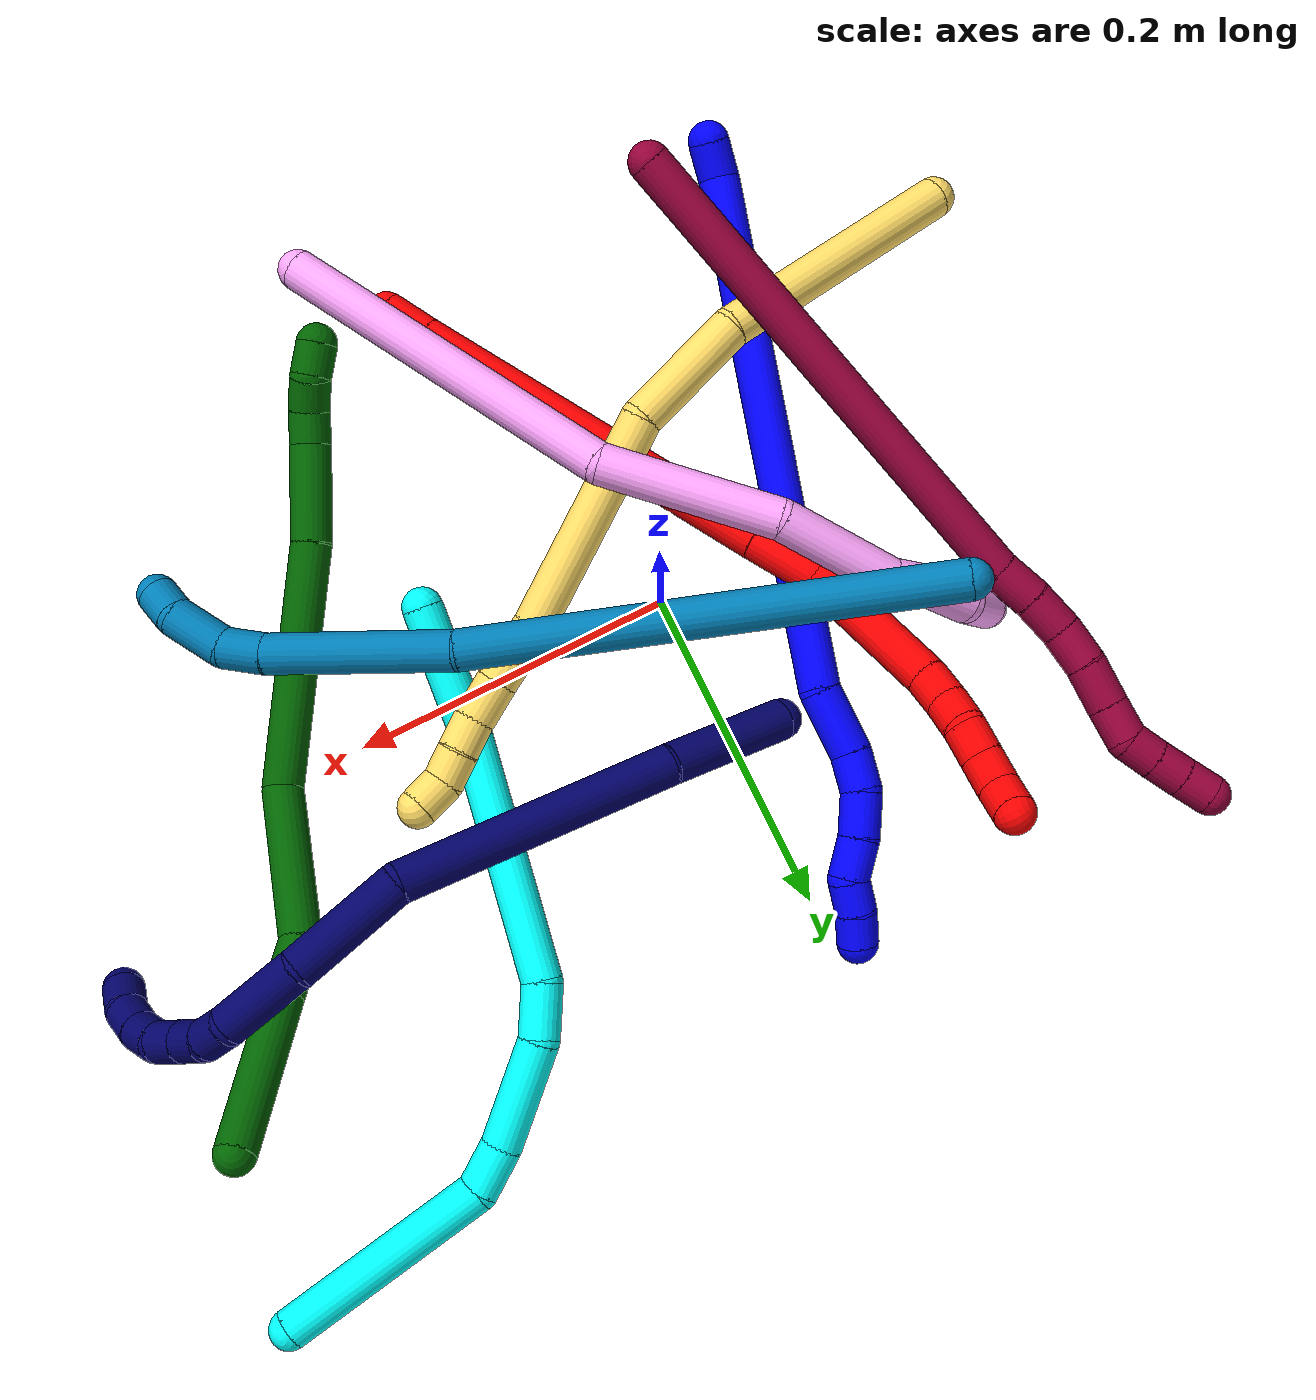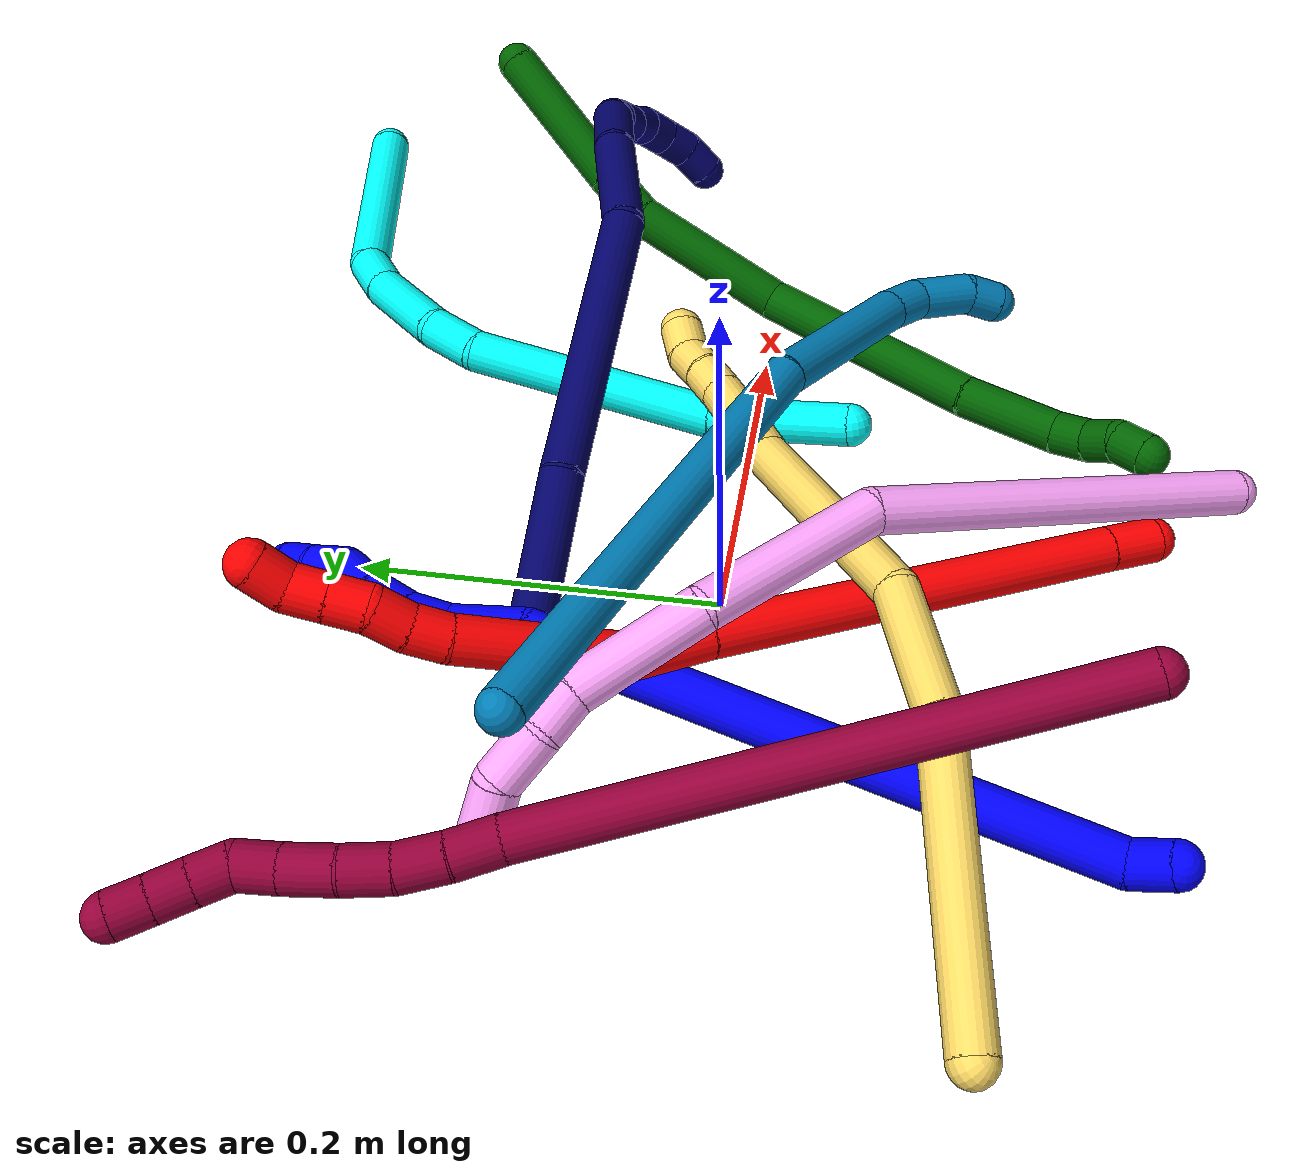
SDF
<sdf version="1.7">
 <world name="default">
  <plugin name="TubeGeneratorPlugin" filename="libtube_generator_plugin.so"/>
  <model name="photoneo_s_sensor">
   <static>1</static>
   <pose>0 0 2 1.57079 1.57079 3.14159</pose>
   <link name="link">
    <inertial><mass>0.1</mass></inertial>
    <sensor name="sensor" type="depth">
     <update_rate>30</update_rate>
     <camera>
      <horizontal_fov>1.22</horizontal_fov>
      <image><width>1920</width><height>1200</height><format>B8G8R8</format></image>
      <clip><near>0.1</near><far>4</far></clip>
      <depth_camera><output>points</output></depth_camera>
     </camera>
     <plugin name="camera_plugin" filename="libgazebo_ros_depth_camera.so">
      <baseline>0.2</baseline>
      <alwaysOn>1</alwaysOn>
      <updateRate>0.0</updateRate>
      <cameraName>camera_ir</cameraName>
      <imageTopicName>/camera/color/image_raw</imageTopicName>
      <cameraInfoTopicName>/camera/color/camera_info</cameraInfoTopicName>
      <depthImageTopicName>/camera/depth/image_raw</depthImageTopicName>
      <depthImageCameraInfoTopicName>/camera/depth/camera_info</depthImageCameraInfoTopicName>
      <pointCloudTopicName>/camera/depth/points</pointCloudTopicName>
      <frameName>fr_optical</frameName>
      <pointCloudCutoff>0.1</pointCloudCutoff>
      <pointCloudCutoffMax>2.0</pointCloudCutoffMax>
      <distortionK1>0</distortionK1>
      <distortionK2>0</distortionK2>
      <distortionK3>0</distortionK3>
      <distortionT1>0</distortionT1>
      <distortionT2>0</distortionT2>
      <CxPrime>0</CxPrime>
      <Cx>0</Cx>
      <Cy>0</Cy>
      <focalLength>0</focalLength>
      <hackBaseline>0</hackBaseline>
     </plugin>
    </sensor>
   </link>
  </model>
  <gravity>0 0 -9.8</gravity>
  <magnetic_field>6e-06 2.3e-05 -4.2e-05</magnetic_field>
  <atmosphere type="adiabatic"/>
  <physics name="default_physics" default="0" type="ode">
   <max_step_size>0.003</max_step_size>
   <real_time_factor>1</real_time_factor>
   <real_time_update_rate>1000</real_time_update_rate>
   <max_contacts>10000</max_contacts>
   <ode>
    <solver>
     <type>quick</type>
     <iters>100</iters>
     <sor>1.3</sor>
     <use_dynamic_moi_rescaling>0</use_dynamic_moi_rescaling>
    </solver>
    <constraints>
     <contact_max_correcting_vel>0</contact_max_correcting_vel>
     <contact_surface_layer>0.001</contact_surface_layer>
     <cfm>0</cfm>
     <erp>0.2</erp>
    </constraints>
   </ode>
  </physics>
  <scene><ambient>0.4 0.4 0.4 1</ambient><background>0.7 0.7 0.7 1</background><shadows>0</shadows></scene>
  <audio><device>default</device></audio>
  <spherical_coordinates>
   <surface_model>EARTH_WGS84</surface_model>
   <latitude_deg>0</latitude_deg>
   <longitude_deg>0</longitude_deg>
   <elevation>0</elevation>
   <heading_deg>0</heading_deg>
  </spherical_coordinates>
  <model name="bin">
   <static>1</static>
   <link name="bottom">
    <collision name="collision-bottom">
     <pose>0 0 -0.01 0 -0 0</pose>
     <geometry><box><size>0.8 0.6 0.02</size></box></geometry>
     <surface>
      <friction><ode><mu>100</mu><mu2>100</mu2></ode></friction>
      <contact><collide_bitmask>65535</collide_bitmask></contact>
     </surface>
    </collision>
   </link>
   <link name="west_wall">
    <collision name="collision-west_wall">
     <pose>-0.41 0 0.1 0 -0 0</pose>
     <geometry><box><size>0.02 0.6 0.2</size></box></geometry>
     <surface>
      <friction><ode><mu>100</mu><mu2>100</mu2></ode></friction>
      <contact><collide_bitmask>65535</collide_bitmask></contact>
     </surface>
    </collision>
   </link>
   <link name="east_wall">
    <collision name="collision-east_wall">
     <pose>0.41 0 0.1 0 -0 0</pose>
     <geometry><box><size>0.02 0.6 0.2</size></box></geometry>
     <surface>
      <friction><ode><mu>100</mu><mu2>100</mu2></ode></friction>
      <contact><collide_bitmask>65535</collide_bitmask></contact>
     </surface>
    </collision>
   </link>
   <link name="south_wall">
    <collision name="collision-south_wall">
     <pose>0 -0.31 0.1 0 -0 0</pose>
     <geometry><box><size>0.8 0.02 0.2</size></box></geometry>
     <surface>
      <friction><ode><mu>100</mu><mu2>100</mu2></ode></friction>
      <contact><collide_bitmask>65535</collide_bitmask></contact>
     </surface>
    </collision>
   </link>
   <link name="north_wall">
    <collision name="collision-north_wall">
     <pose>0 0.31 0.1 0 -0 0</pose>
     <geometry><box><size>0.8 0.02 0.2</size></box></geometry>
     <surface>
      <friction><ode><mu>100</mu><mu2>100</mu2></ode></friction>
      <contact><collide_bitmask>65535</collide_bitmask></contact>
     </surface>
    </collision>
   </link>
  </model>
  <model name="1">
   <static>0</static>
   <link name="1">
    <collision name="collision-cylinder-e_1_1_4">
     <pose>0.001793 0.009902 -0.005923 -2.10984 0.15415 -0.270697</pose>
     <geometry><cylinder><radius>0.0125</radius><length>0.023353</length></cylinder></geometry>
     <surface>
      <friction><ode><mu>1.16</mu><mu2>1.16</mu2><slip1>0</slip1><slip2>0</slip2></ode></friction>
      <contact><ode><kp>1e+06</kp><kd>1</kd><max_vel>0</max_vel><min_depth>0.001</min_depth></ode></contact>
     </surface>
    </collision>
    <visual name="visual-cylinder-e_1_1_4">
     <pose>0.001793 0.009902 -0.005923 -2.10984 0.15415 -0.270697</pose>
     <geometry><cylinder><radius>0.0125</radius><length>0.023353</length></cylinder></geometry>
     <material><ambient>0 0 1 1</ambient></material>
    </visual>
    <collision name="collision-cylinder-e_2_4_5">
     <pose>0.072405 0.161496 -0.038944 -1.75977 0.445119 -0.5343</pose>
     <geometry><cylinder><radius>0.0125</radius><length>0.319669</length></cylinder></geometry>
     <surface>
      <friction><ode><mu>1.16</mu><mu2>1.16</mu2><slip1>0</slip1><slip2>0</slip2></ode></friction>
      <contact><ode><kp>1e+06</kp><kd>1</kd><max_vel>0</max_vel><min_depth>0.001</min_depth></ode></contact>
     </surface>
    </collision>
    <visual name="visual-cylinder-e_2_4_5">
     <pose>0.072405 0.161496 -0.038944 -1.75977 0.445119 -0.5343</pose>
     <geometry><cylinder><radius>0.0125</radius><length>0.319669</length></cylinder></geometry>
     <material><ambient>0 0 1 1</ambient></material>
    </visual>
    <collision name="collision-cylinder-e_3_5_6">
     <pose>0.143889 0.323048 -0.070218 -1.778 0.130573 -0.160758</pose>
     <geometry><cylinder><radius>0.0125</radius><length>0.040936</length></cylinder></geometry>
     <surface>
      <friction><ode><mu>1.16</mu><mu2>1.16</mu2><slip1>0</slip1><slip2>0</slip2></ode></friction>
      <contact><ode><kp>1e+06</kp><kd>1</kd><max_vel>0</max_vel><min_depth>0.001</min_depth></ode></contact>
     </surface>
    </collision>
    <visual name="visual-cylinder-e_3_5_6">
     <pose>0.143889 0.323048 -0.070218 -1.778 0.130573 -0.160758</pose>
     <geometry><cylinder><radius>0.0125</radius><length>0.040936</length></cylinder></geometry>
     <material><ambient>0 0 1 1</ambient></material>
    </visual>
    <collision name="collision-cylinder-e_4_6_7">
     <pose>0.150832 0.353747 -0.076308 -1.74563 0.370662 -0.439777</pose>
     <geometry><cylinder><radius>0.0125</radius><length>0.023621</length></cylinder></geometry>
     <surface>
      <friction><ode><mu>1.16</mu><mu2>1.16</mu2><slip1>0</slip1><slip2>0</slip2></ode></friction>
      <contact><ode><kp>1e+06</kp><kd>1</kd><max_vel>0</max_vel><min_depth>0.001</min_depth></ode></contact>
     </surface>
    </collision>
    <visual name="visual-cylinder-e_4_6_7">
     <pose>0.150832 0.353747 -0.076308 -1.74563 0.370662 -0.439777</pose>
     <geometry><cylinder><radius>0.0125</radius><length>0.023621</length></cylinder></geometry>
     <material><ambient>0 0 1 1</ambient></material>
    </visual>
    <collision name="collision-cylinder-e_5_7_8">
     <pose>0.16307 0.374736 -0.082723 -1.98815 0.622027 -0.917921</pose>
     <geometry><cylinder><radius>0.0125</radius><length>0.02732</length></cylinder></geometry>
     <surface>
      <friction><ode><mu>1.16</mu><mu2>1.16</mu2><slip1>0</slip1><slip2>0</slip2></ode></friction>
      <contact><ode><kp>1e+06</kp><kd>1</kd><max_vel>0</max_vel><min_depth>0.001</min_depth></ode></contact>
     </surface>
    </collision>
    <visual name="visual-cylinder-e_5_7_8">
     <pose>0.16307 0.374736 -0.082723 -1.98815 0.622027 -0.917921</pose>
     <geometry><cylinder><radius>0.0125</radius><length>0.02732</length></cylinder></geometry>
     <material><ambient>0 0 1 1</ambient></material>
    </visual>
    <collision name="collision-cylinder-e_6_8_9">
     <pose>0.179527 0.392421 -0.092339 -2.1672 0.750684 -1.27895</pose>
     <geometry><cylinder><radius>0.0125</radius><length>0.024914</length></cylinder></geometry>
     <surface>
      <friction><ode><mu>1.16</mu><mu2>1.16</mu2><slip1>0</slip1><slip2>0</slip2></ode></friction>
      <contact><ode><kp>1e+06</kp><kd>1</kd><max_vel>0</max_vel><min_depth>0.001</min_depth></ode></contact>
     </surface>
    </collision>
    <visual name="visual-cylinder-e_6_8_9">
     <pose>0.179527 0.392421 -0.092339 -2.1672 0.750684 -1.27895</pose>
     <geometry><cylinder><radius>0.0125</radius><length>0.024914</length></cylinder></geometry>
     <material><ambient>0 0 1 1</ambient></material>
    </visual>
    <collision name="collision-cylinder-e_7_9_10">
     <pose>0.190429 0.408597 -0.102073 -2.0617 0.240753 -0.398285</pose>
     <geometry><cylinder><radius>0.0125</radius><length>0.020174</length></cylinder></geometry>
     <surface>
      <friction><ode><mu>1.16</mu><mu2>1.16</mu2><slip1>0</slip1><slip2>0</slip2></ode></friction>
      <contact><ode><kp>1e+06</kp><kd>1</kd><max_vel>0</max_vel><min_depth>0.001</min_depth></ode></contact>
     </surface>
    </collision>
    <visual name="visual-cylinder-e_7_9_10">
     <pose>0.190429 0.408597 -0.102073 -2.0617 0.240753 -0.398285</pose>
     <geometry><cylinder><radius>0.0125</radius><length>0.020174</length></cylinder></geometry>
     <material><ambient>0 0 1 1</ambient></material>
    </visual>
    <collision name="collision-cylinder-e_8_10_2">
     <pose>0.195998 0.424759 -0.112482 -2.22684 0.321639 -0.63676</pose>
     <geometry><cylinder><radius>0.0125</radius><length>0.020013</length></cylinder></geometry>
     <surface>
      <friction><ode><mu>1.16</mu><mu2>1.16</mu2><slip1>0</slip1><slip2>0</slip2></ode></friction>
      <contact><ode><kp>1e+06</kp><kd>1</kd><max_vel>0</max_vel><min_depth>0.001</min_depth></ode></contact>
     </surface>
    </collision>
    <visual name="visual-cylinder-e_8_10_2">
     <pose>0.195998 0.424759 -0.112482 -2.22684 0.321639 -0.63676</pose>
     <geometry><cylinder><radius>0.0125</radius><length>0.020013</length></cylinder></geometry>
     <material><ambient>0 0 1 1</ambient></material>
    </visual>
    <collision name="collision-sphere-2">
     <pose>0.199161 0.432282 -0.118273 0 -0 0</pose>
     <geometry><sphere><radius>0.0125</radius></sphere></geometry>
     <surface>
      <friction><ode><mu>1.16</mu><mu2>1.16</mu2><slip1>0</slip1><slip2>0</slip2></ode></friction>
      <contact><ode><kp>1e+06</kp><kd>1</kd><max_vel>0</max_vel><min_depth>0.001</min_depth></ode></contact>
     </surface>
    </collision>
    <visual name="visual-sphere-2">
     <pose>0.199161 0.432282 -0.118273 0 -0 0</pose>
     <geometry><sphere><radius>0.0125</radius></sphere></geometry>
     <material><ambient>0 0 1 1</ambient></material>
    </visual>
    <collision name="collision-sphere-10">
     <pose>0.192834 0.417236 -0.106691 0 -0 0</pose>
     <geometry><sphere><radius>0.0125</radius></sphere></geometry>
     <surface>
      <friction><ode><mu>1.16</mu><mu2>1.16</mu2><slip1>0</slip1><slip2>0</slip2></ode></friction>
      <contact><ode><kp>1e+06</kp><kd>1</kd><max_vel>0</max_vel><min_depth>0.001</min_depth></ode></contact>
     </surface>
    </collision>
    <visual name="visual-sphere-10">
     <pose>0.192834 0.417236 -0.106691 0 -0 0</pose>
     <geometry><sphere><radius>0.0125</radius></sphere></geometry>
     <material><ambient>0 0 1 1</ambient></material>
    </visual>
    <collision name="collision-sphere-9">
     <pose>0.188024 0.399958 -0.097455 0 -0 0</pose>
     <geometry><sphere><radius>0.0125</radius></sphere></geometry>
     <surface>
      <friction><ode><mu>1.16</mu><mu2>1.16</mu2><slip1>0</slip1><slip2>0</slip2></ode></friction>
      <contact><ode><kp>1e+06</kp><kd>1</kd><max_vel>0</max_vel><min_depth>0.001</min_depth></ode></contact>
     </surface>
    </collision>
    <visual name="visual-sphere-9">
     <pose>0.188024 0.399958 -0.097455 0 -0 0</pose>
     <geometry><sphere><radius>0.0125</radius></sphere></geometry>
     <material><ambient>0 0 1 1</ambient></material>
    </visual>
    <collision name="collision-sphere-4">
     <pose>0.003586 0.019804 -0.011845 0 -0 0</pose>
     <geometry><sphere><radius>0.0125</radius></sphere></geometry>
     <surface>
      <friction><ode><mu>1.16</mu><mu2>1.16</mu2><slip1>0</slip1><slip2>0</slip2></ode></friction>
      <contact><ode><kp>1e+06</kp><kd>1</kd><max_vel>0</max_vel><min_depth>0.001</min_depth></ode></contact>
     </surface>
    </collision>
    <visual name="visual-sphere-4">
     <pose>0.003586 0.019804 -0.011845 0 -0 0</pose>
     <geometry><sphere><radius>0.0125</radius></sphere></geometry>
     <material><ambient>0 0 1 1</ambient></material>
    </visual>
    <collision name="collision-sphere-1">
     <geometry><sphere><radius>0.0125</radius></sphere></geometry>
     <surface>
      <friction><ode><mu>1.16</mu><mu2>1.16</mu2><slip1>0</slip1><slip2>0</slip2></ode></friction>
      <contact><ode><kp>1e+06</kp><kd>1</kd><max_vel>0</max_vel><min_depth>0.001</min_depth></ode></contact>
     </surface>
    </collision>
    <visual name="visual-sphere-1">
     <geometry><sphere><radius>0.0125</radius></sphere></geometry>
     <material><ambient>0 0 1 1</ambient></material>
    </visual>
    <collision name="collision-sphere-8">
     <pose>0.171029 0.384885 -0.087223 0 -0 0</pose>
     <geometry><sphere><radius>0.0125</radius></sphere></geometry>
     <surface>
      <friction><ode><mu>1.16</mu><mu2>1.16</mu2><slip1>0</slip1><slip2>0</slip2></ode></friction>
      <contact><ode><kp>1e+06</kp><kd>1</kd><max_vel>0</max_vel><min_depth>0.001</min_depth></ode></contact>
     </surface>
    </collision>
    <visual name="visual-sphere-8">
     <pose>0.171029 0.384885 -0.087223 0 -0 0</pose>
     <geometry><sphere><radius>0.0125</radius></sphere></geometry>
     <material><ambient>0 0 1 1</ambient></material>
    </visual>
    <collision name="collision-sphere-5">
     <pose>0.141224 0.303188 -0.066044 0 -0 0</pose>
     <geometry><sphere><radius>0.0125</radius></sphere></geometry>
     <surface>
      <friction><ode><mu>1.16</mu><mu2>1.16</mu2><slip1>0</slip1><slip2>0</slip2></ode></friction>
      <contact><ode><kp>1e+06</kp><kd>1</kd><max_vel>0</max_vel><min_depth>0.001</min_depth></ode></contact>
     </surface>
    </collision>
    <visual name="visual-sphere-5">
     <pose>0.141224 0.303188 -0.066044 0 -0 0</pose>
     <geometry><sphere><radius>0.0125</radius></sphere></geometry>
     <material><ambient>0 0 1 1</ambient></material>
    </visual>
    <collision name="collision-sphere-6">
     <pose>0.146554 0.342907 -0.074393 0 -0 0</pose>
     <geometry><sphere><radius>0.0125</radius></sphere></geometry>
     <surface>
      <friction><ode><mu>1.16</mu><mu2>1.16</mu2><slip1>0</slip1><slip2>0</slip2></ode></friction>
      <contact><ode><kp>1e+06</kp><kd>1</kd><max_vel>0</max_vel><min_depth>0.001</min_depth></ode></contact>
     </surface>
    </collision>
    <visual name="visual-sphere-6">
     <pose>0.146554 0.342907 -0.074393 0 -0 0</pose>
     <geometry><sphere><radius>0.0125</radius></sphere></geometry>
     <material><ambient>0 0 1 1</ambient></material>
    </visual>
    <collision name="collision-sphere-7">
     <pose>0.15511 0.364588 -0.078223 0 -0 0</pose>
     <geometry><sphere><radius>0.0125</radius></sphere></geometry>
     <surface>
      <friction><ode><mu>1.16</mu><mu2>1.16</mu2><slip1>0</slip1><slip2>0</slip2></ode></friction>
      <contact><ode><kp>1e+06</kp><kd>1</kd><max_vel>0</max_vel><min_depth>0.001</min_depth></ode></contact>
     </surface>
    </collision>
    <visual name="visual-sphere-7">
     <pose>0.15511 0.364588 -0.078223 0 -0 0</pose>
     <geometry><sphere><radius>0.0125</radius></sphere></geometry>
     <material><ambient>0 0 1 1</ambient></material>
    </visual>
    <inertial>
     <pose>0.098665 0.22039 -0.052271 0 -0 0</pose>
     <mass>0.5</mass>
     <inertia>
      <ixx>0.000891</ixx>
      <ixy>0</ixy>
      <ixz>0</ixz>
      <iyy>-0.001085</iyy>
      <iyz>0</iyz>
      <izz>-0.003633</izz>
     </inertia>
    </inertial>
   </link>
   <pose>-0.149076 -0.236569 0.019902 0.065143 -0.385436 0.181761</pose>
  </model>
  <model name="2">
   <static>0</static>
   <link name="2">
    <collision name="collision-cylinder-e_1_1_4">
     <pose>-0.001662 0.012624 0.007644 -1.02635 -0.112139 0.06324</pose>
     <geometry><cylinder><radius>0.0125</radius><length>0.029701</length></cylinder></geometry>
     <surface>
      <friction><ode><mu>1.16</mu><mu2>1.16</mu2><slip1>0</slip1><slip2>0</slip2></ode></friction>
      <contact><ode><kp>1e+06</kp><kd>1</kd><max_vel>0</max_vel><min_depth>0.001</min_depth></ode></contact>
     </surface>
    </collision>
    <visual name="visual-cylinder-e_1_1_4">
     <pose>-0.001662 0.012624 0.007644 -1.02635 -0.112139 0.06324</pose>
     <geometry><cylinder><radius>0.0125</radius><length>0.029701</length></cylinder></geometry>
     <material><ambient>1 0 0 1</ambient></material>
    </visual>
    <collision name="collision-cylinder-e_2_4_5">
     <pose>-0.015924 0.124143 0.07879 -0.999979 -0.1068 0.058382</pose>
     <geometry><cylinder><radius>0.0125</radius><length>0.236404</length></cylinder></geometry>
     <surface>
      <friction><ode><mu>1.16</mu><mu2>1.16</mu2><slip1>0</slip1><slip2>0</slip2></ode></friction>
      <contact><ode><kp>1e+06</kp><kd>1</kd><max_vel>0</max_vel><min_depth>0.001</min_depth></ode></contact>
     </surface>
    </collision>
    <visual name="visual-cylinder-e_2_4_5">
     <pose>-0.015924 0.124143 0.07879 -0.999979 -0.1068 0.058382</pose>
     <geometry><cylinder><radius>0.0125</radius><length>0.236404</length></cylinder></geometry>
     <material><ambient>1 0 0 1</ambient></material>
    </visual>
    <collision name="collision-cylinder-e_3_5_6">
     <pose>-0.031841 0.240827 0.15409 -0.985228 -0.15417 0.082868</pose>
     <geometry><cylinder><radius>0.0125</radius><length>0.043202</length></cylinder></geometry>
     <surface>
      <friction><ode><mu>1.16</mu><mu2>1.16</mu2><slip1>0</slip1><slip2>0</slip2></ode></friction>
      <contact><ode><kp>1e+06</kp><kd>1</kd><max_vel>0</max_vel><min_depth>0.001</min_depth></ode></contact>
     </surface>
    </collision>
    <visual name="visual-cylinder-e_3_5_6">
     <pose>-0.031841 0.240827 0.15409 -0.985228 -0.15417 0.082868</pose>
     <geometry><cylinder><radius>0.0125</radius><length>0.043202</length></cylinder></geometry>
     <material><ambient>1 0 0 1</ambient></material>
    </visual>
    <collision name="collision-cylinder-e_4_6_7">
     <pose>-0.028851 0.299595 0.183281 -1.16936 0.140743 -0.093241</pose>
     <geometry><cylinder><radius>0.0125</radius><length>0.089925</length></cylinder></geometry>
     <surface>
      <friction><ode><mu>1.16</mu><mu2>1.16</mu2><slip1>0</slip1><slip2>0</slip2></ode></friction>
      <contact><ode><kp>1e+06</kp><kd>1</kd><max_vel>0</max_vel><min_depth>0.001</min_depth></ode></contact>
     </surface>
    </collision>
    <visual name="visual-cylinder-e_4_6_7">
     <pose>-0.028851 0.299595 0.183281 -1.16936 0.140743 -0.093241</pose>
     <geometry><cylinder><radius>0.0125</radius><length>0.089925</length></cylinder></geometry>
     <material><ambient>1 0 0 1</ambient></material>
    </visual>
    <collision name="collision-cylinder-e_5_7_8">
     <pose>-0.019954 0.350157 0.203383 -1.29549 0.2544 -0.192937</pose>
     <geometry><cylinder><radius>0.0125</radius><length>0.02058</length></cylinder></geometry>
     <surface>
      <friction><ode><mu>1.16</mu><mu2>1.16</mu2><slip1>0</slip1><slip2>0</slip2></ode></friction>
      <contact><ode><kp>1e+06</kp><kd>1</kd><max_vel>0</max_vel><min_depth>0.001</min_depth></ode></contact>
     </surface>
    </collision>
    <visual name="visual-cylinder-e_5_7_8">
     <pose>-0.019954 0.350157 0.203383 -1.29549 0.2544 -0.192937</pose>
     <geometry><cylinder><radius>0.0125</radius><length>0.02058</length></cylinder></geometry>
     <material><ambient>1 0 0 1</ambient></material>
    </visual>
    <collision name="collision-cylinder-e_6_8_9">
     <pose>-0.012827 0.368444 0.208359 -1.31574 0.467188 -0.363648</pose>
     <geometry><cylinder><radius>0.0125</radius><length>0.020147</length></cylinder></geometry>
     <surface>
      <friction><ode><mu>1.16</mu><mu2>1.16</mu2><slip1>0</slip1><slip2>0</slip2></ode></friction>
      <contact><ode><kp>1e+06</kp><kd>1</kd><max_vel>0</max_vel><min_depth>0.001</min_depth></ode></contact>
     </surface>
    </collision>
    <visual name="visual-cylinder-e_6_8_9">
     <pose>-0.012827 0.368444 0.208359 -1.31574 0.467188 -0.363648</pose>
     <geometry><cylinder><radius>0.0125</radius><length>0.020147</length></cylinder></geometry>
     <material><ambient>1 0 0 1</ambient></material>
    </visual>
    <collision name="collision-cylinder-e_7_9_10">
     <pose>-0.006922 0.387011 0.211673 -1.46527 0.137049 -0.123336</pose>
     <geometry><cylinder><radius>0.0125</radius><length>0.020027</length></cylinder></geometry>
     <surface>
      <friction><ode><mu>1.16</mu><mu2>1.16</mu2><slip1>0</slip1><slip2>0</slip2></ode></friction>
      <contact><ode><kp>1e+06</kp><kd>1</kd><max_vel>0</max_vel><min_depth>0.001</min_depth></ode></contact>
     </surface>
    </collision>
    <visual name="visual-cylinder-e_7_9_10">
     <pose>-0.006922 0.387011 0.211673 -1.46527 0.137049 -0.123336</pose>
     <geometry><cylinder><radius>0.0125</radius><length>0.020027</length></cylinder></geometry>
     <material><ambient>1 0 0 1</ambient></material>
    </visual>
    <collision name="collision-cylinder-e_8_10_11">
     <pose>-0.004194 0.40673 0.213741 -1.46738 0.136456 -0.123063</pose>
     <geometry><cylinder><radius>0.0125</radius><length>0.020001</length></cylinder></geometry>
     <surface>
      <friction><ode><mu>1.16</mu><mu2>1.16</mu2><slip1>0</slip1><slip2>0</slip2></ode></friction>
      <contact><ode><kp>1e+06</kp><kd>1</kd><max_vel>0</max_vel><min_depth>0.001</min_depth></ode></contact>
     </surface>
    </collision>
    <visual name="visual-cylinder-e_8_10_11">
     <pose>-0.004194 0.40673 0.213741 -1.46738 0.136456 -0.123063</pose>
     <geometry><cylinder><radius>0.0125</radius><length>0.020001</length></cylinder></geometry>
     <material><ambient>1 0 0 1</ambient></material>
    </visual>
    <collision name="collision-cylinder-e_9_11_2">
     <pose>0.002555 0.424792 0.216697 -1.33943 0.568695 -0.454821</pose>
     <geometry><cylinder><radius>0.0125</radius><length>0.020013</length></cylinder></geometry>
     <surface>
      <friction><ode><mu>1.16</mu><mu2>1.16</mu2><slip1>0</slip1><slip2>0</slip2></ode></friction>
      <contact><ode><kp>1e+06</kp><kd>1</kd><max_vel>0</max_vel><min_depth>0.001</min_depth></ode></contact>
     </surface>
    </collision>
    <visual name="visual-cylinder-e_9_11_2">
     <pose>0.002555 0.424792 0.216697 -1.33943 0.568695 -0.454821</pose>
     <geometry><cylinder><radius>0.0125</radius><length>0.020013</length></cylinder></geometry>
     <material><ambient>1 0 0 1</ambient></material>
    </visual>
    <collision name="collision-sphere-2">
     <pose>0.007944 0.432999 0.218631 0 -0 0</pose>
     <geometry><sphere><radius>0.0125</radius></sphere></geometry>
     <surface>
      <friction><ode><mu>1.16</mu><mu2>1.16</mu2><slip1>0</slip1><slip2>0</slip2></ode></friction>
      <contact><ode><kp>1e+06</kp><kd>1</kd><max_vel>0</max_vel><min_depth>0.001</min_depth></ode></contact>
     </surface>
    </collision>
    <visual name="visual-sphere-2">
     <pose>0.007944 0.432999 0.218631 0 -0 0</pose>
     <geometry><sphere><radius>0.0125</radius></sphere></geometry>
     <material><ambient>1 0 0 1</ambient></material>
    </visual>
    <collision name="collision-sphere-11">
     <pose>-0.002833 0.416585 0.214764 0 -0 0</pose>
     <geometry><sphere><radius>0.0125</radius></sphere></geometry>
     <surface>
      <friction><ode><mu>1.16</mu><mu2>1.16</mu2><slip1>0</slip1><slip2>0</slip2></ode></friction>
      <contact><ode><kp>1e+06</kp><kd>1</kd><max_vel>0</max_vel><min_depth>0.001</min_depth></ode></contact>
     </surface>
    </collision>
    <visual name="visual-sphere-11">
     <pose>-0.002833 0.416585 0.214764 0 -0 0</pose>
     <geometry><sphere><radius>0.0125</radius></sphere></geometry>
     <material><ambient>1 0 0 1</ambient></material>
    </visual>
    <collision name="collision-sphere-10">
     <pose>-0.005554 0.396876 0.212718 0 -0 0</pose>
     <geometry><sphere><radius>0.0125</radius></sphere></geometry>
     <surface>
      <friction><ode><mu>1.16</mu><mu2>1.16</mu2><slip1>0</slip1><slip2>0</slip2></ode></friction>
      <contact><ode><kp>1e+06</kp><kd>1</kd><max_vel>0</max_vel><min_depth>0.001</min_depth></ode></contact>
     </surface>
    </collision>
    <visual name="visual-sphere-10">
     <pose>-0.005554 0.396876 0.212718 0 -0 0</pose>
     <geometry><sphere><radius>0.0125</radius></sphere></geometry>
     <material><ambient>1 0 0 1</ambient></material>
    </visual>
    <collision name="collision-sphere-9">
     <pose>-0.00829 0.377147 0.210629 0 -0 0</pose>
     <geometry><sphere><radius>0.0125</radius></sphere></geometry>
     <surface>
      <friction><ode><mu>1.16</mu><mu2>1.16</mu2><slip1>0</slip1><slip2>0</slip2></ode></friction>
      <contact><ode><kp>1e+06</kp><kd>1</kd><max_vel>0</max_vel><min_depth>0.001</min_depth></ode></contact>
     </surface>
    </collision>
    <visual name="visual-sphere-9">
     <pose>-0.00829 0.377147 0.210629 0 -0 0</pose>
     <geometry><sphere><radius>0.0125</radius></sphere></geometry>
     <material><ambient>1 0 0 1</ambient></material>
    </visual>
    <collision name="collision-sphere-4">
     <pose>-0.003324 0.025248 0.015287 0 -0 0</pose>
     <geometry><sphere><radius>0.0125</radius></sphere></geometry>
     <surface>
      <friction><ode><mu>1.16</mu><mu2>1.16</mu2><slip1>0</slip1><slip2>0</slip2></ode></friction>
      <contact><ode><kp>1e+06</kp><kd>1</kd><max_vel>0</max_vel><min_depth>0.001</min_depth></ode></contact>
     </surface>
    </collision>
    <visual name="visual-sphere-4">
     <pose>-0.003324 0.025248 0.015287 0 -0 0</pose>
     <geometry><sphere><radius>0.0125</radius></sphere></geometry>
     <material><ambient>1 0 0 1</ambient></material>
    </visual>
    <collision name="collision-sphere-1">
     <geometry><sphere><radius>0.0125</radius></sphere></geometry>
     <surface>
      <friction><ode><mu>1.16</mu><mu2>1.16</mu2><slip1>0</slip1><slip2>0</slip2></ode></friction>
      <contact><ode><kp>1e+06</kp><kd>1</kd><max_vel>0</max_vel><min_depth>0.001</min_depth></ode></contact>
     </surface>
    </collision>
    <visual name="visual-sphere-1">
     <geometry><sphere><radius>0.0125</radius></sphere></geometry>
     <material><ambient>1 0 0 1</ambient></material>
    </visual>
    <collision name="collision-sphere-8">
     <pose>-0.017364 0.359741 0.20609 0 -0 0</pose>
     <geometry><sphere><radius>0.0125</radius></sphere></geometry>
     <surface>
      <friction><ode><mu>1.16</mu><mu2>1.16</mu2><slip1>0</slip1><slip2>0</slip2></ode></friction>
      <contact><ode><kp>1e+06</kp><kd>1</kd><max_vel>0</max_vel><min_depth>0.001</min_depth></ode></contact>
     </surface>
    </collision>
    <visual name="visual-sphere-8">
     <pose>-0.017364 0.359741 0.20609 0 -0 0</pose>
     <geometry><sphere><radius>0.0125</radius></sphere></geometry>
     <material><ambient>1 0 0 1</ambient></material>
    </visual>
    <collision name="collision-sphere-5">
     <pose>-0.028524 0.223038 0.142293 0 -0 0</pose>
     <geometry><sphere><radius>0.0125</radius></sphere></geometry>
     <surface>
      <friction><ode><mu>1.16</mu><mu2>1.16</mu2><slip1>0</slip1><slip2>0</slip2></ode></friction>
      <contact><ode><kp>1e+06</kp><kd>1</kd><max_vel>0</max_vel><min_depth>0.001</min_depth></ode></contact>
     </surface>
    </collision>
    <visual name="visual-sphere-5">
     <pose>-0.028524 0.223038 0.142293 0 -0 0</pose>
     <geometry><sphere><radius>0.0125</radius></sphere></geometry>
     <material><ambient>1 0 0 1</ambient></material>
    </visual>
    <collision name="collision-sphere-6">
     <pose>-0.035158 0.258616 0.165886 0 -0 0</pose>
     <geometry><sphere><radius>0.0125</radius></sphere></geometry>
     <surface>
      <friction><ode><mu>1.16</mu><mu2>1.16</mu2><slip1>0</slip1><slip2>0</slip2></ode></friction>
      <contact><ode><kp>1e+06</kp><kd>1</kd><max_vel>0</max_vel><min_depth>0.001</min_depth></ode></contact>
     </surface>
    </collision>
    <visual name="visual-sphere-6">
     <pose>-0.035158 0.258616 0.165886 0 -0 0</pose>
     <geometry><sphere><radius>0.0125</radius></sphere></geometry>
     <material><ambient>1 0 0 1</ambient></material>
    </visual>
    <collision name="collision-sphere-7">
     <pose>-0.022543 0.340573 0.200676 0 -0 0</pose>
     <geometry><sphere><radius>0.0125</radius></sphere></geometry>
     <surface>
      <friction><ode><mu>1.16</mu><mu2>1.16</mu2><slip1>0</slip1><slip2>0</slip2></ode></friction>
      <contact><ode><kp>1e+06</kp><kd>1</kd><max_vel>0</max_vel><min_depth>0.001</min_depth></ode></contact>
     </surface>
    </collision>
    <visual name="visual-sphere-7">
     <pose>-0.022543 0.340573 0.200676 0 -0 0</pose>
     <geometry><sphere><radius>0.0125</radius></sphere></geometry>
     <material><ambient>1 0 0 1</ambient></material>
    </visual>
    <inertial>
     <pose>-0.017248 0.212169 0.126452 0 -0 0</pose>
     <mass>0.5</mass>
     <inertia>
      <ixx>0.001242</ixx>
      <ixy>0</ixy>
      <ixz>0</ixz>
      <iyy>0.00073</iyy>
      <iyz>0</iyz>
      <izz>-0.000878</izz>
     </inertia>
    </inertial>
   </link>
   <pose>0.070719 -0.230432 0.011963 0.246203 -1.24076 -0.278368</pose>
  </model>
  <model name="3">
   <static>0</static>
   <link name="3">
    <collision name="collision-cylinder-e_1_1_4">
     <pose>-0.025022 0.033314 -0.004319 -1.69972 -0.640206 0.721491</pose>
     <geometry><cylinder><radius>0.0125</radius><length>0.083776</length></cylinder></geometry>
     <surface>
      <friction><ode><mu>1.16</mu><mu2>1.16</mu2><slip1>0</slip1><slip2>0</slip2></ode></friction>
      <contact><ode><kp>1e+06</kp><kd>1</kd><max_vel>0</max_vel><min_depth>0.001</min_depth></ode></contact>
     </surface>
    </collision>
    <visual name="visual-cylinder-e_1_1_4">
     <pose>-0.025022 0.033314 -0.004319 -1.69972 -0.640206 0.721491</pose>
     <geometry><cylinder><radius>0.0125</radius><length>0.083776</length></cylinder></geometry>
     <material><ambient>0.003922 1 0.996078 1</ambient></material>
    </visual>
    <collision name="collision-cylinder-e_2_4_5">
     <pose>-0.091348 0.124429 -0.033437 -1.9761 -0.581064 0.851745</pose>
     <geometry><cylinder><radius>0.0125</radius><length>0.15049</length></cylinder></geometry>
     <surface>
      <friction><ode><mu>1.16</mu><mu2>1.16</mu2><slip1>0</slip1><slip2>0</slip2></ode></friction>
      <contact><ode><kp>1e+06</kp><kd>1</kd><max_vel>0</max_vel><min_depth>0.001</min_depth></ode></contact>
     </surface>
    </collision>
    <visual name="visual-cylinder-e_2_4_5">
     <pose>-0.091348 0.124429 -0.033437 -1.9761 -0.581064 0.851745</pose>
     <geometry><cylinder><radius>0.0125</radius><length>0.15049</length></cylinder></geometry>
     <material><ambient>0.003922 1 0.996078 1</ambient></material>
    </visual>
    <collision name="collision-cylinder-e_3_5_6">
     <pose>-0.145451 0.190828 -0.064892 -2.22944 -0.8666 1.51216</pose>
     <geometry><cylinder><radius>0.0125</radius><length>0.033592</length></cylinder></geometry>
     <surface>
      <friction><ode><mu>1.16</mu><mu2>1.16</mu2><slip1>0</slip1><slip2>0</slip2></ode></friction>
      <contact><ode><kp>1e+06</kp><kd>1</kd><max_vel>0</max_vel><min_depth>0.001</min_depth></ode></contact>
     </surface>
    </collision>
    <visual name="visual-cylinder-e_3_5_6">
     <pose>-0.145451 0.190828 -0.064892 -2.22944 -0.8666 1.51216</pose>
     <geometry><cylinder><radius>0.0125</radius><length>0.033592</length></cylinder></geometry>
     <material><ambient>0.003922 1 0.996078 1</ambient></material>
    </visual>
    <collision name="collision-cylinder-e_4_6_7">
     <pose>-0.189661 0.206951 -0.080785 -2.45817 -1.20825 2.18997</pose>
     <geometry><cylinder><radius>0.0125</radius><length>0.067184</length></cylinder></geometry>
     <surface>
      <friction><ode><mu>1.16</mu><mu2>1.16</mu2><slip1>0</slip1><slip2>0</slip2></ode></friction>
      <contact><ode><kp>1e+06</kp><kd>1</kd><max_vel>0</max_vel><min_depth>0.001</min_depth></ode></contact>
     </surface>
    </collision>
    <visual name="visual-cylinder-e_4_6_7">
     <pose>-0.189661 0.206951 -0.080785 -2.45817 -1.20825 2.18997</pose>
     <geometry><cylinder><radius>0.0125</radius><length>0.067184</length></cylinder></geometry>
     <material><ambient>0.003922 1 0.996078 1</ambient></material>
    </visual>
    <collision name="collision-cylinder-e_5_7_8">
     <pose>-0.234577 0.215945 -0.096362 -2.91355 -1.12191 2.781</pose>
     <geometry><cylinder><radius>0.0125</radius><length>0.029988</length></cylinder></geometry>
     <surface>
      <friction><ode><mu>1.16</mu><mu2>1.16</mu2><slip1>0</slip1><slip2>0</slip2></ode></friction>
      <contact><ode><kp>1e+06</kp><kd>1</kd><max_vel>0</max_vel><min_depth>0.001</min_depth></ode></contact>
     </surface>
    </collision>
    <visual name="visual-cylinder-e_5_7_8">
     <pose>-0.234577 0.215945 -0.096362 -2.91355 -1.12191 2.781</pose>
     <geometry><cylinder><radius>0.0125</radius><length>0.029988</length></cylinder></geometry>
     <material><ambient>0.003922 1 0.996078 1</ambient></material>
    </visual>
    <collision name="collision-cylinder-e_6_8_2">
     <pose>-0.303803 0.194037 -0.132755 2.4805 -0.971296 -1.98868</pose>
     <geometry><cylinder><radius>0.0125</radius><length>0.13497</length></cylinder></geometry>
     <surface>
      <friction><ode><mu>1.16</mu><mu2>1.16</mu2><slip1>0</slip1><slip2>0</slip2></ode></friction>
      <contact><ode><kp>1e+06</kp><kd>1</kd><max_vel>0</max_vel><min_depth>0.001</min_depth></ode></contact>
     </surface>
    </collision>
    <visual name="visual-cylinder-e_6_8_2">
     <pose>-0.303803 0.194037 -0.132755 2.4805 -0.971296 -1.98868</pose>
     <geometry><cylinder><radius>0.0125</radius><length>0.13497</length></cylinder></geometry>
     <material><ambient>0.003922 1 0.996078 1</ambient></material>
    </visual>
    <collision name="collision-sphere-2">
     <pose>-0.359519 0.170658 -0.16281 0 -0 0</pose>
     <geometry><sphere><radius>0.0125</radius></sphere></geometry>
     <surface>
      <friction><ode><mu>1.16</mu><mu2>1.16</mu2><slip1>0</slip1><slip2>0</slip2></ode></friction>
      <contact><ode><kp>1e+06</kp><kd>1</kd><max_vel>0</max_vel><min_depth>0.001</min_depth></ode></contact>
     </surface>
    </collision>
    <visual name="visual-sphere-2">
     <pose>-0.359519 0.170658 -0.16281 0 -0 0</pose>
     <geometry><sphere><radius>0.0125</radius></sphere></geometry>
     <material><ambient>0.003922 1 0.996078 1</ambient></material>
    </visual>
    <collision name="collision-sphere-4">
     <pose>-0.050045 0.066629 -0.008638 0 -0 0</pose>
     <geometry><sphere><radius>0.0125</radius></sphere></geometry>
     <surface>
      <friction><ode><mu>1.16</mu><mu2>1.16</mu2><slip1>0</slip1><slip2>0</slip2></ode></friction>
      <contact><ode><kp>1e+06</kp><kd>1</kd><max_vel>0</max_vel><min_depth>0.001</min_depth></ode></contact>
     </surface>
    </collision>
    <visual name="visual-sphere-4">
     <pose>-0.050045 0.066629 -0.008638 0 -0 0</pose>
     <geometry><sphere><radius>0.0125</radius></sphere></geometry>
     <material><ambient>0.003922 1 0.996078 1</ambient></material>
    </visual>
    <collision name="collision-sphere-1">
     <geometry><sphere><radius>0.0125</radius></sphere></geometry>
     <surface>
      <friction><ode><mu>1.16</mu><mu2>1.16</mu2><slip1>0</slip1><slip2>0</slip2></ode></friction>
      <contact><ode><kp>1e+06</kp><kd>1</kd><max_vel>0</max_vel><min_depth>0.001</min_depth></ode></contact>
     </surface>
    </collision>
    <visual name="visual-sphere-1">
     <geometry><sphere><radius>0.0125</radius></sphere></geometry>
     <material><ambient>0.003922 1 0.996078 1</ambient></material>
    </visual>
    <collision name="collision-sphere-8">
     <pose>-0.248086 0.217416 -0.1027 0 -0 0</pose>
     <geometry><sphere><radius>0.0125</radius></sphere></geometry>
     <surface>
      <friction><ode><mu>1.16</mu><mu2>1.16</mu2><slip1>0</slip1><slip2>0</slip2></ode></friction>
      <contact><ode><kp>1e+06</kp><kd>1</kd><max_vel>0</max_vel><min_depth>0.001</min_depth></ode></contact>
     </surface>
    </collision>
    <visual name="visual-sphere-8">
     <pose>-0.248086 0.217416 -0.1027 0 -0 0</pose>
     <geometry><sphere><radius>0.0125</radius></sphere></geometry>
     <material><ambient>0.003922 1 0.996078 1</ambient></material>
    </visual>
    <collision name="collision-sphere-5">
     <pose>-0.132651 0.182229 -0.058237 0 -0 0</pose>
     <geometry><sphere><radius>0.0125</radius></sphere></geometry>
     <surface>
      <friction><ode><mu>1.16</mu><mu2>1.16</mu2><slip1>0</slip1><slip2>0</slip2></ode></friction>
      <contact><ode><kp>1e+06</kp><kd>1</kd><max_vel>0</max_vel><min_depth>0.001</min_depth></ode></contact>
     </surface>
    </collision>
    <visual name="visual-sphere-5">
     <pose>-0.132651 0.182229 -0.058237 0 -0 0</pose>
     <geometry><sphere><radius>0.0125</radius></sphere></geometry>
     <material><ambient>0.003922 1 0.996078 1</ambient></material>
    </visual>
    <collision name="collision-sphere-6">
     <pose>-0.158252 0.199428 -0.071547 0 -0 0</pose>
     <geometry><sphere><radius>0.0125</radius></sphere></geometry>
     <surface>
      <friction><ode><mu>1.16</mu><mu2>1.16</mu2><slip1>0</slip1><slip2>0</slip2></ode></friction>
      <contact><ode><kp>1e+06</kp><kd>1</kd><max_vel>0</max_vel><min_depth>0.001</min_depth></ode></contact>
     </surface>
    </collision>
    <visual name="visual-sphere-6">
     <pose>-0.158252 0.199428 -0.071547 0 -0 0</pose>
     <geometry><sphere><radius>0.0125</radius></sphere></geometry>
     <material><ambient>0.003922 1 0.996078 1</ambient></material>
    </visual>
    <collision name="collision-sphere-7">
     <pose>-0.221069 0.214474 -0.090024 0 -0 0</pose>
     <geometry><sphere><radius>0.0125</radius></sphere></geometry>
     <surface>
      <friction><ode><mu>1.16</mu><mu2>1.16</mu2><slip1>0</slip1><slip2>0</slip2></ode></friction>
      <contact><ode><kp>1e+06</kp><kd>1</kd><max_vel>0</max_vel><min_depth>0.001</min_depth></ode></contact>
     </surface>
    </collision>
    <visual name="visual-sphere-7">
     <pose>-0.221069 0.214474 -0.090024 0 -0 0</pose>
     <geometry><sphere><radius>0.0125</radius></sphere></geometry>
     <material><ambient>0.003922 1 0.996078 1</ambient></material>
    </visual>
    <inertial>
     <pose>-0.16302 0.14899 -0.067618 0 -0 0</pose>
     <mass>0.5</mass>
     <inertia>
      <ixx>0.000221</ixx>
      <ixy>0</ixy>
      <ixz>0</ixz>
      <iyy>0.000373</iyy>
      <iyz>0</iyz>
      <izz>0.000183</izz>
     </inertia>
    </inertial>
   </link>
   <pose>0.12959 -0.05752 0.022565 3.0808 -0.475081 -2.58845</pose>
  </model>
  <model name="4">
   <static>0</static>
   <link name="4">
    <collision name="collision-cylinder-e_1_1_4">
     <pose>0.023816 0.093178 -0.06592 -2.18651 0.205707 -0.393751</pose>
     <geometry><cylinder><radius>0.0125</radius><length>0.233194</length></cylinder></geometry>
     <surface>
      <friction><ode><mu>1.16</mu><mu2>1.16</mu2><slip1>0</slip1><slip2>0</slip2></ode></friction>
      <contact><ode><kp>1e+06</kp><kd>1</kd><max_vel>0</max_vel><min_depth>0.001</min_depth></ode></contact>
     </surface>
    </collision>
    <visual name="visual-cylinder-e_1_1_4">
     <pose>0.023816 0.093178 -0.06592 -2.18651 0.205707 -0.393751</pose>
     <geometry><cylinder><radius>0.0125</radius><length>0.233194</length></cylinder></geometry>
     <material><ambient>1 0.65098 0.996078 1</ambient></material>
    </visual>
    <collision name="collision-cylinder-e_2_4_5">
     <pose>0.044116 0.219089 -0.175114 -2.49399 -0.064717 0.192305</pose>
     <geometry><cylinder><radius>0.0125</radius><length>0.108744</length></cylinder></geometry>
     <surface>
      <friction><ode><mu>1.16</mu><mu2>1.16</mu2><slip1>0</slip1><slip2>0</slip2></ode></friction>
      <contact><ode><kp>1e+06</kp><kd>1</kd><max_vel>0</max_vel><min_depth>0.001</min_depth></ode></contact>
     </surface>
    </collision>
    <visual name="visual-cylinder-e_2_4_5">
     <pose>0.044116 0.219089 -0.175114 -2.49399 -0.064717 0.192305</pose>
     <geometry><cylinder><radius>0.0125</radius><length>0.108744</length></cylinder></geometry>
     <material><ambient>1 0.65098 0.996078 1</ambient></material>
    </visual>
    <collision name="collision-cylinder-e_3_5_6">
     <pose>0.045039 0.265428 -0.2524 -2.76107 0.120592 -0.607515</pose>
     <geometry><cylinder><radius>0.0125</radius><length>0.073803</length></cylinder></geometry>
     <surface>
      <friction><ode><mu>1.16</mu><mu2>1.16</mu2><slip1>0</slip1><slip2>0</slip2></ode></friction>
      <contact><ode><kp>1e+06</kp><kd>1</kd><max_vel>0</max_vel><min_depth>0.001</min_depth></ode></contact>
     </surface>
    </collision>
    <visual name="visual-cylinder-e_3_5_6">
     <pose>0.045039 0.265428 -0.2524 -2.76107 0.120592 -0.607515</pose>
     <geometry><cylinder><radius>0.0125</radius><length>0.073803</length></cylinder></geometry>
     <material><ambient>1 0.65098 0.996078 1</ambient></material>
    </visual>
    <collision name="collision-cylinder-e_4_6_7">
     <pose>0.047434 0.281729 -0.298037 -2.9137 -0.169667 1.2781</pose>
     <geometry><cylinder><radius>0.0125</radius><length>0.024213</length></cylinder></geometry>
     <surface>
      <friction><ode><mu>1.16</mu><mu2>1.16</mu2><slip1>0</slip1><slip2>0</slip2></ode></friction>
      <contact><ode><kp>1e+06</kp><kd>1</kd><max_vel>0</max_vel><min_depth>0.001</min_depth></ode></contact>
     </surface>
    </collision>
    <visual name="visual-cylinder-e_4_6_7">
     <pose>0.047434 0.281729 -0.298037 -2.9137 -0.169667 1.2781</pose>
     <geometry><cylinder><radius>0.0125</radius><length>0.024213</length></cylinder></geometry>
     <material><ambient>1 0.65098 0.996078 1</ambient></material>
    </visual>
    <collision name="collision-cylinder-e_5_7_8">
     <pose>0.045589 0.285149 -0.325013 -3.09447 0.012984 -0.537649</pose>
     <geometry><cylinder><radius>0.0125</radius><length>0.030739</length></cylinder></geometry>
     <surface>
      <friction><ode><mu>1.16</mu><mu2>1.16</mu2><slip1>0</slip1><slip2>0</slip2></ode></friction>
      <contact><ode><kp>1e+06</kp><kd>1</kd><max_vel>0</max_vel><min_depth>0.001</min_depth></ode></contact>
     </surface>
    </collision>
    <visual name="visual-cylinder-e_5_7_8">
     <pose>0.045589 0.285149 -0.325013 -3.09447 0.012984 -0.537649</pose>
     <geometry><cylinder><radius>0.0125</radius><length>0.030739</length></cylinder></geometry>
     <material><ambient>1 0.65098 0.996078 1</ambient></material>
    </visual>
    <collision name="collision-cylinder-e_6_8_2">
     <pose>0.044535 0.280041 -0.353747 2.73062 -0.085632 -0.40545</pose>
     <geometry><cylinder><radius>0.0125</radius><length>0.029306</length></cylinder></geometry>
     <surface>
      <friction><ode><mu>1.16</mu><mu2>1.16</mu2><slip1>0</slip1><slip2>0</slip2></ode></friction>
      <contact><ode><kp>1e+06</kp><kd>1</kd><max_vel>0</max_vel><min_depth>0.001</min_depth></ode></contact>
     </surface>
    </collision>
    <visual name="visual-cylinder-e_6_8_2">
     <pose>0.044535 0.280041 -0.353747 2.73062 -0.085632 -0.40545</pose>
     <geometry><cylinder><radius>0.0125</radius><length>0.029306</length></cylinder></geometry>
     <material><ambient>1 0.65098 0.996078 1</ambient></material>
    </visual>
    <collision name="collision-sphere-2">
     <pose>0.043282 0.274208 -0.367131 0 -0 0</pose>
     <geometry><sphere><radius>0.0125</radius></sphere></geometry>
     <surface>
      <friction><ode><mu>1.16</mu><mu2>1.16</mu2><slip1>0</slip1><slip2>0</slip2></ode></friction>
      <contact><ode><kp>1e+06</kp><kd>1</kd><max_vel>0</max_vel><min_depth>0.001</min_depth></ode></contact>
     </surface>
    </collision>
    <visual name="visual-sphere-2">
     <pose>0.043282 0.274208 -0.367131 0 -0 0</pose>
     <geometry><sphere><radius>0.0125</radius></sphere></geometry>
     <material><ambient>1 0.65098 0.996078 1</ambient></material>
    </visual>
    <collision name="collision-sphere-4">
     <pose>0.047632 0.186357 -0.131841 0 -0 0</pose>
     <geometry><sphere><radius>0.0125</radius></sphere></geometry>
     <surface>
      <friction><ode><mu>1.16</mu><mu2>1.16</mu2><slip1>0</slip1><slip2>0</slip2></ode></friction>
      <contact><ode><kp>1e+06</kp><kd>1</kd><max_vel>0</max_vel><min_depth>0.001</min_depth></ode></contact>
     </surface>
    </collision>
    <visual name="visual-sphere-4">
     <pose>0.047632 0.186357 -0.131841 0 -0 0</pose>
     <geometry><sphere><radius>0.0125</radius></sphere></geometry>
     <material><ambient>1 0.65098 0.996078 1</ambient></material>
    </visual>
    <collision name="collision-sphere-1">
     <geometry><sphere><radius>0.0125</radius></sphere></geometry>
     <surface>
      <friction><ode><mu>1.16</mu><mu2>1.16</mu2><slip1>0</slip1><slip2>0</slip2></ode></friction>
      <contact><ode><kp>1e+06</kp><kd>1</kd><max_vel>0</max_vel><min_depth>0.001</min_depth></ode></contact>
     </surface>
    </collision>
    <visual name="visual-sphere-1">
     <geometry><sphere><radius>0.0125</radius></sphere></geometry>
     <material><ambient>1 0.65098 0.996078 1</ambient></material>
    </visual>
    <collision name="collision-sphere-8">
     <pose>0.045789 0.285873 -0.340364 0 -0 0</pose>
     <geometry><sphere><radius>0.0125</radius></sphere></geometry>
     <surface>
      <friction><ode><mu>1.16</mu><mu2>1.16</mu2><slip1>0</slip1><slip2>0</slip2></ode></friction>
      <contact><ode><kp>1e+06</kp><kd>1</kd><max_vel>0</max_vel><min_depth>0.001</min_depth></ode></contact>
     </surface>
    </collision>
    <visual name="visual-sphere-8">
     <pose>0.045789 0.285873 -0.340364 0 -0 0</pose>
     <geometry><sphere><radius>0.0125</radius></sphere></geometry>
     <material><ambient>1 0.65098 0.996078 1</ambient></material>
    </visual>
    <collision name="collision-sphere-5">
     <pose>0.040599 0.251822 -0.218387 0 -0 0</pose>
     <geometry><sphere><radius>0.0125</radius></sphere></geometry>
     <surface>
      <friction><ode><mu>1.16</mu><mu2>1.16</mu2><slip1>0</slip1><slip2>0</slip2></ode></friction>
      <contact><ode><kp>1e+06</kp><kd>1</kd><max_vel>0</max_vel><min_depth>0.001</min_depth></ode></contact>
     </surface>
    </collision>
    <visual name="visual-sphere-5">
     <pose>0.040599 0.251822 -0.218387 0 -0 0</pose>
     <geometry><sphere><radius>0.0125</radius></sphere></geometry>
     <material><ambient>1 0.65098 0.996078 1</ambient></material>
    </visual>
    <collision name="collision-sphere-6">
     <pose>0.049478 0.279034 -0.286413 0 -0 0</pose>
     <geometry><sphere><radius>0.0125</radius></sphere></geometry>
     <surface>
      <friction><ode><mu>1.16</mu><mu2>1.16</mu2><slip1>0</slip1><slip2>0</slip2></ode></friction>
      <contact><ode><kp>1e+06</kp><kd>1</kd><max_vel>0</max_vel><min_depth>0.001</min_depth></ode></contact>
     </surface>
    </collision>
    <visual name="visual-sphere-6">
     <pose>0.049478 0.279034 -0.286413 0 -0 0</pose>
     <geometry><sphere><radius>0.0125</radius></sphere></geometry>
     <material><ambient>1 0.65098 0.996078 1</ambient></material>
    </visual>
    <collision name="collision-sphere-7">
     <pose>0.045389 0.284425 -0.309662 0 -0 0</pose>
     <geometry><sphere><radius>0.0125</radius></sphere></geometry>
     <surface>
      <friction><ode><mu>1.16</mu><mu2>1.16</mu2><slip1>0</slip1><slip2>0</slip2></ode></friction>
      <contact><ode><kp>1e+06</kp><kd>1</kd><max_vel>0</max_vel><min_depth>0.001</min_depth></ode></contact>
     </surface>
    </collision>
    <visual name="visual-sphere-7">
     <pose>0.045389 0.284425 -0.309662 0 -0 0</pose>
     <geometry><sphere><radius>0.0125</radius></sphere></geometry>
     <material><ambient>1 0.65098 0.996078 1</ambient></material>
    </visual>
    <inertial>
     <pose>0.03506 0.177873 -0.161233 0 -0 0</pose>
     <mass>0.5</mass>
     <inertia>
      <ixx>0.000712</ixx>
      <ixy>0</ixy>
      <ixz>0</ixz>
      <iyy>-0.000999</iyy>
      <iyz>0</iyz>
      <izz>-0.001175</izz>
     </inertia>
    </inertial>
   </link>
   <pose>0.107325 -0.275227 0.01951 0.923698 0.1259 0.745602</pose>
  </model>
  <model name="5">
   <static>0</static>
   <link name="5">
    <collision name="collision-cylinder-e_1_1_4">
     <pose>0.074936 0.028104 0.008711 -1.27024 1.19665 -0.931108</pose>
     <geometry><cylinder><radius>0.0125</radius><length>0.161011</length></cylinder></geometry>
     <surface>
      <friction><ode><mu>1.16</mu><mu2>1.16</mu2><slip1>0</slip1><slip2>0</slip2></ode></friction>
      <contact><ode><kp>1e+06</kp><kd>1</kd><max_vel>0</max_vel><min_depth>0.001</min_depth></ode></contact>
     </surface>
    </collision>
    <visual name="visual-cylinder-e_1_1_4">
     <pose>0.074936 0.028104 0.008711 -1.27024 1.19665 -0.931108</pose>
     <geometry><cylinder><radius>0.0125</radius><length>0.161011</length></cylinder></geometry>
     <material><ambient>1 0.858824 0.4 1</ambient></material>
    </visual>
    <collision name="collision-cylinder-e_2_4_5">
     <pose>0.184969 0.069731 0.01149 -1.9842 1.17254 -1.58728</pose>
     <geometry><cylinder><radius>0.0125</radius><length>0.076155</length></cylinder></geometry>
     <surface>
      <friction><ode><mu>1.16</mu><mu2>1.16</mu2><slip1>0</slip1><slip2>0</slip2></ode></friction>
      <contact><ode><kp>1e+06</kp><kd>1</kd><max_vel>0</max_vel><min_depth>0.001</min_depth></ode></contact>
     </surface>
    </collision>
    <visual name="visual-cylinder-e_2_4_5">
     <pose>0.184969 0.069731 0.01149 -1.9842 1.17254 -1.58728</pose>
     <geometry><cylinder><radius>0.0125</radius><length>0.076155</length></cylinder></geometry>
     <material><ambient>1 0.858824 0.4 1</ambient></material>
    </visual>
    <collision name="collision-cylinder-e_3_5_6">
     <pose>0.273841 0.108723 -0.027222 -2.48104 0.913399 -1.92317</pose>
     <geometry><cylinder><radius>0.0125</radius><length>0.135864</length></cylinder></geometry>
     <surface>
      <friction><ode><mu>1.16</mu><mu2>1.16</mu2><slip1>0</slip1><slip2>0</slip2></ode></friction>
      <contact><ode><kp>1e+06</kp><kd>1</kd><max_vel>0</max_vel><min_depth>0.001</min_depth></ode></contact>
     </surface>
    </collision>
    <visual name="visual-cylinder-e_3_5_6">
     <pose>0.273841 0.108723 -0.027222 -2.48104 0.913399 -1.92317</pose>
     <geometry><cylinder><radius>0.0125</radius><length>0.135864</length></cylinder></geometry>
     <material><ambient>1 0.858824 0.4 1</ambient></material>
    </visual>
    <collision name="collision-cylinder-e_4_6_7">
     <pose>0.344231 0.14063 -0.068044 -2.46668 1.01575 -2.01662</pose>
     <geometry><cylinder><radius>0.0125</radius><length>0.039101</length></cylinder></geometry>
     <surface>
      <friction><ode><mu>1.16</mu><mu2>1.16</mu2><slip1>0</slip1><slip2>0</slip2></ode></friction>
      <contact><ode><kp>1e+06</kp><kd>1</kd><max_vel>0</max_vel><min_depth>0.001</min_depth></ode></contact>
     </surface>
    </collision>
    <visual name="visual-cylinder-e_4_6_7">
     <pose>0.344231 0.14063 -0.068044 -2.46668 1.01575 -2.01662</pose>
     <geometry><cylinder><radius>0.0125</radius><length>0.039101</length></cylinder></geometry>
     <material><ambient>1 0.858824 0.4 1</ambient></material>
    </visual>
    <collision name="collision-cylinder-e_5_7_8">
     <pose>0.371727 0.152157 -0.081324 -2.37036 0.979702 -1.84017</pose>
     <geometry><cylinder><radius>0.0125</radius><length>0.026208</length></cylinder></geometry>
     <surface>
      <friction><ode><mu>1.16</mu><mu2>1.16</mu2><slip1>0</slip1><slip2>0</slip2></ode></friction>
      <contact><ode><kp>1e+06</kp><kd>1</kd><max_vel>0</max_vel><min_depth>0.001</min_depth></ode></contact>
     </surface>
    </collision>
    <visual name="visual-cylinder-e_5_7_8">
     <pose>0.371727 0.152157 -0.081324 -2.37036 0.979702 -1.84017</pose>
     <geometry><cylinder><radius>0.0125</radius><length>0.026208</length></cylinder></geometry>
     <material><ambient>1 0.858824 0.4 1</ambient></material>
    </visual>
    <collision name="collision-cylinder-e_6_8_9">
     <pose>0.390573 0.162444 -0.090536 -2.22377 0.883152 -1.52657</pose>
     <geometry><cylinder><radius>0.0125</radius><length>0.020617</length></cylinder></geometry>
     <surface>
      <friction><ode><mu>1.16</mu><mu2>1.16</mu2><slip1>0</slip1><slip2>0</slip2></ode></friction>
      <contact><ode><kp>1e+06</kp><kd>1</kd><max_vel>0</max_vel><min_depth>0.001</min_depth></ode></contact>
     </surface>
    </collision>
    <visual name="visual-cylinder-e_6_8_9">
     <pose>0.390573 0.162444 -0.090536 -2.22377 0.883152 -1.52657</pose>
     <geometry><cylinder><radius>0.0125</radius><length>0.020617</length></cylinder></geometry>
     <material><ambient>1 0.858824 0.4 1</ambient></material>
    </visual>
    <collision name="collision-cylinder-e_7_9_10">
     <pose>0.406349 0.171912 -0.09924 -2.40696 0.886485 -1.77938</pose>
     <geometry><cylinder><radius>0.0125</radius><length>0.02016</length></cylinder></geometry>
     <surface>
      <friction><ode><mu>1.16</mu><mu2>1.16</mu2><slip1>0</slip1><slip2>0</slip2></ode></friction>
      <contact><ode><kp>1e+06</kp><kd>1</kd><max_vel>0</max_vel><min_depth>0.001</min_depth></ode></contact>
     </surface>
    </collision>
    <visual name="visual-cylinder-e_7_9_10">
     <pose>0.406349 0.171912 -0.09924 -2.40696 0.886485 -1.77938</pose>
     <geometry><cylinder><radius>0.0125</radius><length>0.02016</length></cylinder></geometry>
     <material><ambient>1 0.858824 0.4 1</ambient></material>
    </visual>
    <collision name="collision-cylinder-e_8_10_2">
     <pose>0.423612 0.180535 -0.104838 -1.76804 1.13182 -1.31827</pose>
     <geometry><cylinder><radius>0.0125</radius><length>0.020884</length></cylinder></geometry>
     <surface>
      <friction><ode><mu>1.16</mu><mu2>1.16</mu2><slip1>0</slip1><slip2>0</slip2></ode></friction>
      <contact><ode><kp>1e+06</kp><kd>1</kd><max_vel>0</max_vel><min_depth>0.001</min_depth></ode></contact>
     </surface>
    </collision>
    <visual name="visual-cylinder-e_8_10_2">
     <pose>0.423612 0.180535 -0.104838 -1.76804 1.13182 -1.31827</pose>
     <geometry><cylinder><radius>0.0125</radius><length>0.020884</length></cylinder></geometry>
     <material><ambient>1 0.858824 0.4 1</ambient></material>
    </visual>
    <collision name="collision-sphere-2">
     <pose>0.433064 0.184887 -0.105707 0 -0 0</pose>
     <geometry><sphere><radius>0.0125</radius></sphere></geometry>
     <surface>
      <friction><ode><mu>1.16</mu><mu2>1.16</mu2><slip1>0</slip1><slip2>0</slip2></ode></friction>
      <contact><ode><kp>1e+06</kp><kd>1</kd><max_vel>0</max_vel><min_depth>0.001</min_depth></ode></contact>
     </surface>
    </collision>
    <visual name="visual-sphere-2">
     <pose>0.433064 0.184887 -0.105707 0 -0 0</pose>
     <geometry><sphere><radius>0.0125</radius></sphere></geometry>
     <material><ambient>1 0.858824 0.4 1</ambient></material>
    </visual>
    <collision name="collision-sphere-10">
     <pose>0.41416 0.176183 -0.103968 0 -0 0</pose>
     <geometry><sphere><radius>0.0125</radius></sphere></geometry>
     <surface>
      <friction><ode><mu>1.16</mu><mu2>1.16</mu2><slip1>0</slip1><slip2>0</slip2></ode></friction>
      <contact><ode><kp>1e+06</kp><kd>1</kd><max_vel>0</max_vel><min_depth>0.001</min_depth></ode></contact>
     </surface>
    </collision>
    <visual name="visual-sphere-10">
     <pose>0.41416 0.176183 -0.103968 0 -0 0</pose>
     <geometry><sphere><radius>0.0125</radius></sphere></geometry>
     <material><ambient>1 0.858824 0.4 1</ambient></material>
    </visual>
    <collision name="collision-sphere-9">
     <pose>0.398539 0.167641 -0.094511 0 -0 0</pose>
     <geometry><sphere><radius>0.0125</radius></sphere></geometry>
     <surface>
      <friction><ode><mu>1.16</mu><mu2>1.16</mu2><slip1>0</slip1><slip2>0</slip2></ode></friction>
      <contact><ode><kp>1e+06</kp><kd>1</kd><max_vel>0</max_vel><min_depth>0.001</min_depth></ode></contact>
     </surface>
    </collision>
    <visual name="visual-sphere-9">
     <pose>0.398539 0.167641 -0.094511 0 -0 0</pose>
     <geometry><sphere><radius>0.0125</radius></sphere></geometry>
     <material><ambient>1 0.858824 0.4 1</ambient></material>
    </visual>
    <collision name="collision-sphere-4">
     <pose>0.149872 0.056209 0.017422 0 -0 0</pose>
     <geometry><sphere><radius>0.0125</radius></sphere></geometry>
     <surface>
      <friction><ode><mu>1.16</mu><mu2>1.16</mu2><slip1>0</slip1><slip2>0</slip2></ode></friction>
      <contact><ode><kp>1e+06</kp><kd>1</kd><max_vel>0</max_vel><min_depth>0.001</min_depth></ode></contact>
     </surface>
    </collision>
    <visual name="visual-sphere-4">
     <pose>0.149872 0.056209 0.017422 0 -0 0</pose>
     <geometry><sphere><radius>0.0125</radius></sphere></geometry>
     <material><ambient>1 0.858824 0.4 1</ambient></material>
    </visual>
    <collision name="collision-sphere-1">
     <geometry><sphere><radius>0.0125</radius></sphere></geometry>
     <surface>
      <friction><ode><mu>1.16</mu><mu2>1.16</mu2><slip1>0</slip1><slip2>0</slip2></ode></friction>
      <contact><ode><kp>1e+06</kp><kd>1</kd><max_vel>0</max_vel><min_depth>0.001</min_depth></ode></contact>
     </surface>
    </collision>
    <visual name="visual-sphere-1">
     <geometry><sphere><radius>0.0125</radius></sphere></geometry>
     <material><ambient>1 0.858824 0.4 1</ambient></material>
    </visual>
    <collision name="collision-sphere-8">
     <pose>0.382607 0.157247 -0.086561 0 -0 0</pose>
     <geometry><sphere><radius>0.0125</radius></sphere></geometry>
     <surface>
      <friction><ode><mu>1.16</mu><mu2>1.16</mu2><slip1>0</slip1><slip2>0</slip2></ode></friction>
      <contact><ode><kp>1e+06</kp><kd>1</kd><max_vel>0</max_vel><min_depth>0.001</min_depth></ode></contact>
     </surface>
    </collision>
    <visual name="visual-sphere-8">
     <pose>0.382607 0.157247 -0.086561 0 -0 0</pose>
     <geometry><sphere><radius>0.0125</radius></sphere></geometry>
     <material><ambient>1 0.858824 0.4 1</ambient></material>
    </visual>
    <collision name="collision-sphere-5">
     <pose>0.220067 0.083254 0.005557 0 -0 0</pose>
     <geometry><sphere><radius>0.0125</radius></sphere></geometry>
     <surface>
      <friction><ode><mu>1.16</mu><mu2>1.16</mu2><slip1>0</slip1><slip2>0</slip2></ode></friction>
      <contact><ode><kp>1e+06</kp><kd>1</kd><max_vel>0</max_vel><min_depth>0.001</min_depth></ode></contact>
     </surface>
    </collision>
    <visual name="visual-sphere-5">
     <pose>0.220067 0.083254 0.005557 0 -0 0</pose>
     <geometry><sphere><radius>0.0125</radius></sphere></geometry>
     <material><ambient>1 0.858824 0.4 1</ambient></material>
    </visual>
    <collision name="collision-sphere-6">
     <pose>0.327615 0.134192 -0.06 0 -0 0</pose>
     <geometry><sphere><radius>0.0125</radius></sphere></geometry>
     <surface>
      <friction><ode><mu>1.16</mu><mu2>1.16</mu2><slip1>0</slip1><slip2>0</slip2></ode></friction>
      <contact><ode><kp>1e+06</kp><kd>1</kd><max_vel>0</max_vel><min_depth>0.001</min_depth></ode></contact>
     </surface>
    </collision>
    <visual name="visual-sphere-6">
     <pose>0.327615 0.134192 -0.06 0 -0 0</pose>
     <geometry><sphere><radius>0.0125</radius></sphere></geometry>
     <material><ambient>1 0.858824 0.4 1</ambient></material>
    </visual>
    <collision name="collision-sphere-7">
     <pose>0.360846 0.147067 -0.076088 0 -0 0</pose>
     <geometry><sphere><radius>0.0125</radius></sphere></geometry>
     <surface>
      <friction><ode><mu>1.16</mu><mu2>1.16</mu2><slip1>0</slip1><slip2>0</slip2></ode></friction>
      <contact><ode><kp>1e+06</kp><kd>1</kd><max_vel>0</max_vel><min_depth>0.001</min_depth></ode></contact>
     </surface>
    </collision>
    <visual name="visual-sphere-7">
     <pose>0.360846 0.147067 -0.076088 0 -0 0</pose>
     <geometry><sphere><radius>0.0125</radius></sphere></geometry>
     <material><ambient>1 0.858824 0.4 1</ambient></material>
    </visual>
    <inertial>
     <pose>0.2233 0.089357 -0.024539 0 -0 0</pose>
     <mass>0.5</mass>
     <inertia>
      <ixx>-0.000185</ixx>
      <ixy>0</ixy>
      <ixz>0</ixz>
      <iyy>0.000281</iyy>
      <iyz>0</iyz>
      <izz>-0.000779</izz>
     </inertia>
    </inertial>
   </link>
   <pose>-0.257337 -0.147267 0.011497 0.711084 0.030825 -0.027722</pose>
  </model>
  <model name="6">
   <static>0</static>
   <link name="6">
    <collision name="collision-cylinder-e_1_1_4">
     <pose>-0.028558 -0.038671 -0.007267 1.75655 -0.627825 -0.746035</pose>
     <geometry><cylinder><radius>0.0125</radius><length>0.097239</length></cylinder></geometry>
     <surface>
      <friction><ode><mu>1.16</mu><mu2>1.16</mu2><slip1>0</slip1><slip2>0</slip2></ode></friction>
      <contact><ode><kp>1e+06</kp><kd>1</kd><max_vel>0</max_vel><min_depth>0.001</min_depth></ode></contact>
     </surface>
    </collision>
    <visual name="visual-cylinder-e_1_1_4">
     <pose>-0.028558 -0.038671 -0.007267 1.75655 -0.627825 -0.746035</pose>
     <geometry><cylinder><radius>0.0125</radius><length>0.097239</length></cylinder></geometry>
     <material><ambient>0 0.392157 0.003922 1</ambient></material>
    </visual>
    <collision name="collision-cylinder-e_2_4_5">
     <pose>-0.067928 -0.090792 -0.015013 1.60636 -0.676759 -0.699345</pose>
     <geometry><cylinder><radius>0.0125</radius><length>0.034527</length></cylinder></geometry>
     <surface>
      <friction><ode><mu>1.16</mu><mu2>1.16</mu2><slip1>0</slip1><slip2>0</slip2></ode></friction>
      <contact><ode><kp>1e+06</kp><kd>1</kd><max_vel>0</max_vel><min_depth>0.001</min_depth></ode></contact>
     </surface>
    </collision>
    <visual name="visual-cylinder-e_2_4_5">
     <pose>-0.067928 -0.090792 -0.015013 1.60636 -0.676759 -0.699345</pose>
     <geometry><cylinder><radius>0.0125</radius><length>0.034527</length></cylinder></geometry>
     <material><ambient>0 0.392157 0.003922 1</ambient></material>
    </visual>
    <collision name="collision-cylinder-e_3_5_6">
     <pose>-0.09208 -0.151942 -0.018797 1.63999 -0.272087 -0.291332</pose>
     <geometry><cylinder><radius>0.0125</radius><length>0.09928</length></cylinder></geometry>
     <surface>
      <friction><ode><mu>1.16</mu><mu2>1.16</mu2><slip1>0</slip1><slip2>0</slip2></ode></friction>
      <contact><ode><kp>1e+06</kp><kd>1</kd><max_vel>0</max_vel><min_depth>0.001</min_depth></ode></contact>
     </surface>
    </collision>
    <visual name="visual-cylinder-e_3_5_6">
     <pose>-0.09208 -0.151942 -0.018797 1.63999 -0.272087 -0.291332</pose>
     <geometry><cylinder><radius>0.0125</radius><length>0.09928</length></cylinder></geometry>
     <material><ambient>0 0.392157 0.003922 1</ambient></material>
    </visual>
    <collision name="collision-cylinder-e_4_6_7">
     <pose>-0.14213 -0.257791 0.004723 1.13856 -0.520504 -0.337586</pose>
     <geometry><cylinder><radius>0.0125</radius><length>0.147629</length></cylinder></geometry>
     <surface>
      <friction><ode><mu>1.16</mu><mu2>1.16</mu2><slip1>0</slip1><slip2>0</slip2></ode></friction>
      <contact><ode><kp>1e+06</kp><kd>1</kd><max_vel>0</max_vel><min_depth>0.001</min_depth></ode></contact>
     </surface>
    </collision>
    <visual name="visual-cylinder-e_4_6_7">
     <pose>-0.14213 -0.257791 0.004723 1.13856 -0.520504 -0.337586</pose>
     <geometry><cylinder><radius>0.0125</radius><length>0.147629</length></cylinder></geometry>
     <material><ambient>0 0.392157 0.003922 1</ambient></material>
    </visual>
    <collision name="collision-cylinder-e_5_7_8">
     <pose>-0.190462 -0.34119 0.042341 1.16688 -0.400424 -0.266322</pose>
     <geometry><cylinder><radius>0.0125</radius><length>0.059635</length></cylinder></geometry>
     <surface>
      <friction><ode><mu>1.16</mu><mu2>1.16</mu2><slip1>0</slip1><slip2>0</slip2></ode></friction>
      <contact><ode><kp>1e+06</kp><kd>1</kd><max_vel>0</max_vel><min_depth>0.001</min_depth></ode></contact>
     </surface>
    </collision>
    <visual name="visual-cylinder-e_5_7_8">
     <pose>-0.190462 -0.34119 0.042341 1.16688 -0.400424 -0.266322</pose>
     <geometry><cylinder><radius>0.0125</radius><length>0.059635</length></cylinder></geometry>
     <material><ambient>0 0.392157 0.003922 1</ambient></material>
    </visual>
    <collision name="collision-cylinder-e_6_8_9">
     <pose>-0.205689 -0.374646 0.058412 0.999108 -0.353768 -0.194483</pose>
     <geometry><cylinder><radius>0.0125</radius><length>0.020805</length></cylinder></geometry>
     <surface>
      <friction><ode><mu>1.16</mu><mu2>1.16</mu2><slip1>0</slip1><slip2>0</slip2></ode></friction>
      <contact><ode><kp>1e+06</kp><kd>1</kd><max_vel>0</max_vel><min_depth>0.001</min_depth></ode></contact>
     </surface>
    </collision>
    <visual name="visual-cylinder-e_6_8_9">
     <pose>-0.205689 -0.374646 0.058412 0.999108 -0.353768 -0.194483</pose>
     <geometry><cylinder><radius>0.0125</radius><length>0.020805</length></cylinder></geometry>
     <material><ambient>0 0.392157 0.003922 1</ambient></material>
    </visual>
    <collision name="collision-cylinder-e_7_9_10">
     <pose>-0.2131 -0.388217 0.071781 0.585695 -0.373754 -0.1139</pose>
     <geometry><cylinder><radius>0.0125</radius><length>0.020852</length></cylinder></geometry>
     <surface>
      <friction><ode><mu>1.16</mu><mu2>1.16</mu2><slip1>0</slip1><slip2>0</slip2></ode></friction>
      <contact><ode><kp>1e+06</kp><kd>1</kd><max_vel>0</max_vel><min_depth>0.001</min_depth></ode></contact>
     </surface>
    </collision>
    <visual name="visual-cylinder-e_7_9_10">
     <pose>-0.2131 -0.388217 0.071781 0.585695 -0.373754 -0.1139</pose>
     <geometry><cylinder><radius>0.0125</radius><length>0.020852</length></cylinder></geometry>
     <material><ambient>0 0.392157 0.003922 1</ambient></material>
    </visual>
    <collision name="collision-cylinder-e_8_10_2">
     <pose>-0.222455 -0.400663 0.084276 1.01407 -0.587103 -0.332716</pose>
     <geometry><cylinder><radius>0.0125</radius><length>0.020033</length></cylinder></geometry>
     <surface>
      <friction><ode><mu>1.16</mu><mu2>1.16</mu2><slip1>0</slip1><slip2>0</slip2></ode></friction>
      <contact><ode><kp>1e+06</kp><kd>1</kd><max_vel>0</max_vel><min_depth>0.001</min_depth></ode></contact>
     </surface>
    </collision>
    <visual name="visual-cylinder-e_8_10_2">
     <pose>-0.222455 -0.400663 0.084276 1.01407 -0.587103 -0.332716</pose>
     <geometry><cylinder><radius>0.0125</radius><length>0.020033</length></cylinder></geometry>
     <material><ambient>0 0.392157 0.003922 1</ambient></material>
    </visual>
    <collision name="collision-sphere-2">
     <pose>-0.228004 -0.407743 0.088682 0 -0 0</pose>
     <geometry><sphere><radius>0.0125</radius></sphere></geometry>
     <surface>
      <friction><ode><mu>1.16</mu><mu2>1.16</mu2><slip1>0</slip1><slip2>0</slip2></ode></friction>
      <contact><ode><kp>1e+06</kp><kd>1</kd><max_vel>0</max_vel><min_depth>0.001</min_depth></ode></contact>
     </surface>
    </collision>
    <visual name="visual-sphere-2">
     <pose>-0.228004 -0.407743 0.088682 0 -0 0</pose>
     <geometry><sphere><radius>0.0125</radius></sphere></geometry>
     <material><ambient>0 0.392157 0.003922 1</ambient></material>
    </visual>
    <collision name="collision-sphere-10">
     <pose>-0.216906 -0.393583 0.079869 0 -0 0</pose>
     <geometry><sphere><radius>0.0125</radius></sphere></geometry>
     <surface>
      <friction><ode><mu>1.16</mu><mu2>1.16</mu2><slip1>0</slip1><slip2>0</slip2></ode></friction>
      <contact><ode><kp>1e+06</kp><kd>1</kd><max_vel>0</max_vel><min_depth>0.001</min_depth></ode></contact>
     </surface>
    </collision>
    <visual name="visual-sphere-10">
     <pose>-0.216906 -0.393583 0.079869 0 -0 0</pose>
     <geometry><sphere><radius>0.0125</radius></sphere></geometry>
     <material><ambient>0 0.392157 0.003922 1</ambient></material>
    </visual>
    <collision name="collision-sphere-9">
     <pose>-0.209293 -0.382852 0.063692 0 -0 0</pose>
     <geometry><sphere><radius>0.0125</radius></sphere></geometry>
     <surface>
      <friction><ode><mu>1.16</mu><mu2>1.16</mu2><slip1>0</slip1><slip2>0</slip2></ode></friction>
      <contact><ode><kp>1e+06</kp><kd>1</kd><max_vel>0</max_vel><min_depth>0.001</min_depth></ode></contact>
     </surface>
    </collision>
    <visual name="visual-sphere-9">
     <pose>-0.209293 -0.382852 0.063692 0 -0 0</pose>
     <geometry><sphere><radius>0.0125</radius></sphere></geometry>
     <material><ambient>0 0.392157 0.003922 1</ambient></material>
    </visual>
    <collision name="collision-sphere-4">
     <pose>-0.057117 -0.077342 -0.014534 0 -0 0</pose>
     <geometry><sphere><radius>0.0125</radius></sphere></geometry>
     <surface>
      <friction><ode><mu>1.16</mu><mu2>1.16</mu2><slip1>0</slip1><slip2>0</slip2></ode></friction>
      <contact><ode><kp>1e+06</kp><kd>1</kd><max_vel>0</max_vel><min_depth>0.001</min_depth></ode></contact>
     </surface>
    </collision>
    <visual name="visual-sphere-4">
     <pose>-0.057117 -0.077342 -0.014534 0 -0 0</pose>
     <geometry><sphere><radius>0.0125</radius></sphere></geometry>
     <material><ambient>0 0.392157 0.003922 1</ambient></material>
    </visual>
    <collision name="collision-sphere-1">
     <geometry><sphere><radius>0.0125</radius></sphere></geometry>
     <surface>
      <friction><ode><mu>1.16</mu><mu2>1.16</mu2><slip1>0</slip1><slip2>0</slip2></ode></friction>
      <contact><ode><kp>1e+06</kp><kd>1</kd><max_vel>0</max_vel><min_depth>0.001</min_depth></ode></contact>
     </surface>
    </collision>
    <visual name="visual-sphere-1">
     <geometry><sphere><radius>0.0125</radius></sphere></geometry>
     <material><ambient>0 0.392157 0.003922 1</ambient></material>
    </visual>
    <collision name="collision-sphere-8">
     <pose>-0.202085 -0.366439 0.053133 0 -0 0</pose>
     <geometry><sphere><radius>0.0125</radius></sphere></geometry>
     <surface>
      <friction><ode><mu>1.16</mu><mu2>1.16</mu2><slip1>0</slip1><slip2>0</slip2></ode></friction>
      <contact><ode><kp>1e+06</kp><kd>1</kd><max_vel>0</max_vel><min_depth>0.001</min_depth></ode></contact>
     </surface>
    </collision>
    <visual name="visual-sphere-8">
     <pose>-0.202085 -0.366439 0.053133 0 -0 0</pose>
     <geometry><sphere><radius>0.0125</radius></sphere></geometry>
     <material><ambient>0 0.392157 0.003922 1</ambient></material>
    </visual>
    <collision name="collision-sphere-5">
     <pose>-0.07874 -0.104242 -0.015491 0 -0 0</pose>
     <geometry><sphere><radius>0.0125</radius></sphere></geometry>
     <surface>
      <friction><ode><mu>1.16</mu><mu2>1.16</mu2><slip1>0</slip1><slip2>0</slip2></ode></friction>
      <contact><ode><kp>1e+06</kp><kd>1</kd><max_vel>0</max_vel><min_depth>0.001</min_depth></ode></contact>
     </surface>
    </collision>
    <visual name="visual-sphere-5">
     <pose>-0.07874 -0.104242 -0.015491 0 -0 0</pose>
     <geometry><sphere><radius>0.0125</radius></sphere></geometry>
     <material><ambient>0 0.392157 0.003922 1</ambient></material>
    </visual>
    <collision name="collision-sphere-6">
     <pose>-0.105421 -0.199641 -0.022103 0 -0 0</pose>
     <geometry><sphere><radius>0.0125</radius></sphere></geometry>
     <surface>
      <friction><ode><mu>1.16</mu><mu2>1.16</mu2><slip1>0</slip1><slip2>0</slip2></ode></friction>
      <contact><ode><kp>1e+06</kp><kd>1</kd><max_vel>0</max_vel><min_depth>0.001</min_depth></ode></contact>
     </surface>
    </collision>
    <visual name="visual-sphere-6">
     <pose>-0.105421 -0.199641 -0.022103 0 -0 0</pose>
     <geometry><sphere><radius>0.0125</radius></sphere></geometry>
     <material><ambient>0 0.392157 0.003922 1</ambient></material>
    </visual>
    <collision name="collision-sphere-7">
     <pose>-0.178839 -0.315941 0.031549 0 -0 0</pose>
     <geometry><sphere><radius>0.0125</radius></sphere></geometry>
     <surface>
      <friction><ode><mu>1.16</mu><mu2>1.16</mu2><slip1>0</slip1><slip2>0</slip2></ode></friction>
      <contact><ode><kp>1e+06</kp><kd>1</kd><max_vel>0</max_vel><min_depth>0.001</min_depth></ode></contact>
     </surface>
    </collision>
    <visual name="visual-sphere-7">
     <pose>-0.178839 -0.315941 0.031549 0 -0 0</pose>
     <geometry><sphere><radius>0.0125</radius></sphere></geometry>
     <material><ambient>0 0.392157 0.003922 1</ambient></material>
    </visual>
    <inertial>
     <pose>-0.119568 -0.208601 0.009063 0 -0 0</pose>
     <mass>0.5</mass>
     <inertia><ixx>0.000203</ixx><ixy>0</ixy><ixz>0</ixz><iyy>-1e-06</iyy><iyz>0</iyz><izz>0.000612</izz></inertia>
    </inertial>
   </link>
   <pose>0.348893 0.181697 0.109917 0.313677 -0.160644 -0.03361</pose>
  </model>
  <model name="7">
   <static>0</static>
   <link name="7">
    <collision name="collision-cylinder-e_1_1_4">
     <pose>0.008572 -0.002482 0.039606 0.062584 0.212745 0.006685</pose>
     <geometry><cylinder><radius>0.0125</radius><length>0.081199</length></cylinder></geometry>
     <surface>
      <friction><ode><mu>1.16</mu><mu2>1.16</mu2><slip1>0</slip1><slip2>0</slip2></ode></friction>
      <contact><ode><kp>1e+06</kp><kd>1</kd><max_vel>0</max_vel><min_depth>0.001</min_depth></ode></contact>
     </surface>
    </collision>
    <visual name="visual-cylinder-e_1_1_4">
     <pose>0.008572 -0.002482 0.039606 0.062584 0.212745 0.006685</pose>
     <geometry><cylinder><radius>0.0125</radius><length>0.081199</length></cylinder></geometry>
     <material><ambient>0.003922 0 0.403922 1</ambient></material>
    </visual>
    <collision name="collision-cylinder-e_2_4_5">
     <pose>0.051329 -0.008265 0.158875 0.041418 0.405042 0.008506</pose>
     <geometry><cylinder><radius>0.0125</radius><length>0.1735</length></cylinder></geometry>
     <surface>
      <friction><ode><mu>1.16</mu><mu2>1.16</mu2><slip1>0</slip1><slip2>0</slip2></ode></friction>
      <contact><ode><kp>1e+06</kp><kd>1</kd><max_vel>0</max_vel><min_depth>0.001</min_depth></ode></contact>
     </surface>
    </collision>
    <visual name="visual-cylinder-e_2_4_5">
     <pose>0.051329 -0.008265 0.158875 0.041418 0.405042 0.008506</pose>
     <geometry><cylinder><radius>0.0125</radius><length>0.1735</length></cylinder></geometry>
     <material><ambient>0.003922 0 0.403922 1</ambient></material>
    </visual>
    <collision name="collision-cylinder-e_3_5_6">
     <pose>0.10558 -0.002107 0.267251 -0.318256 0.586002 -0.096756</pose>
     <geometry><cylinder><radius>0.0125</radius><length>0.072569</length></cylinder></geometry>
     <surface>
      <friction><ode><mu>1.16</mu><mu2>1.16</mu2><slip1>0</slip1><slip2>0</slip2></ode></friction>
      <contact><ode><kp>1e+06</kp><kd>1</kd><max_vel>0</max_vel><min_depth>0.001</min_depth></ode></contact>
     </surface>
    </collision>
    <visual name="visual-cylinder-e_3_5_6">
     <pose>0.10558 -0.002107 0.267251 -0.318256 0.586002 -0.096756</pose>
     <geometry><cylinder><radius>0.0125</radius><length>0.072569</length></cylinder></geometry>
     <material><ambient>0.003922 0 0.403922 1</ambient></material>
    </visual>
    <collision name="collision-cylinder-e_4_6_7">
     <pose>0.145529 0.013493 0.312017 -0.365348 0.857965 -0.16859</pose>
     <geometry><cylinder><radius>0.0125</radius><length>0.052563</length></cylinder></geometry>
     <surface>
      <friction><ode><mu>1.16</mu><mu2>1.16</mu2><slip1>0</slip1><slip2>0</slip2></ode></friction>
      <contact><ode><kp>1e+06</kp><kd>1</kd><max_vel>0</max_vel><min_depth>0.001</min_depth></ode></contact>
     </surface>
    </collision>
    <visual name="visual-cylinder-e_4_6_7">
     <pose>0.145529 0.013493 0.312017 -0.365348 0.857965 -0.16859</pose>
     <geometry><cylinder><radius>0.0125</radius><length>0.052563</length></cylinder></geometry>
     <material><ambient>0.003922 0 0.403922 1</ambient></material>
    </visual>
    <collision name="collision-cylinder-e_5_7_8">
     <pose>0.174863 0.020911 0.331153 -0.392803 1.23134 -0.279657</pose>
     <geometry><cylinder><radius>0.0125</radius><length>0.020047</length></cylinder></geometry>
     <surface>
      <friction><ode><mu>1.16</mu><mu2>1.16</mu2><slip1>0</slip1><slip2>0</slip2></ode></friction>
      <contact><ode><kp>1e+06</kp><kd>1</kd><max_vel>0</max_vel><min_depth>0.001</min_depth></ode></contact>
     </surface>
    </collision>
    <visual name="visual-cylinder-e_5_7_8">
     <pose>0.174863 0.020911 0.331153 -0.392803 1.23134 -0.279657</pose>
     <geometry><cylinder><radius>0.0125</radius><length>0.020047</length></cylinder></geometry>
     <material><ambient>0.003922 0 0.403922 1</ambient></material>
    </visual>
    <collision name="collision-cylinder-e_6_8_9">
     <pose>0.194049 0.020087 0.335507 1.02702 1.32365 0.827933</pose>
     <geometry><cylinder><radius>0.0125</radius><length>0.020079</length></cylinder></geometry>
     <surface>
      <friction><ode><mu>1.16</mu><mu2>1.16</mu2><slip1>0</slip1><slip2>0</slip2></ode></friction>
      <contact><ode><kp>1e+06</kp><kd>1</kd><max_vel>0</max_vel><min_depth>0.001</min_depth></ode></contact>
     </surface>
    </collision>
    <visual name="visual-cylinder-e_6_8_9">
     <pose>0.194049 0.020087 0.335507 1.02702 1.32365 0.827933</pose>
     <geometry><cylinder><radius>0.0125</radius><length>0.020079</length></cylinder></geometry>
     <material><ambient>0.003922 0 0.403922 1</ambient></material>
    </visual>
    <collision name="collision-cylinder-e_7_9_10">
     <pose>0.213028 0.015166 0.339361 0.82902 1.17862 0.572194</pose>
     <geometry><cylinder><radius>0.0125</radius><length>0.02001</length></cylinder></geometry>
     <surface>
      <friction><ode><mu>1.16</mu><mu2>1.16</mu2><slip1>0</slip1><slip2>0</slip2></ode></friction>
      <contact><ode><kp>1e+06</kp><kd>1</kd><max_vel>0</max_vel><min_depth>0.001</min_depth></ode></contact>
     </surface>
    </collision>
    <visual name="visual-cylinder-e_7_9_10">
     <pose>0.213028 0.015166 0.339361 0.82902 1.17862 0.572194</pose>
     <geometry><cylinder><radius>0.0125</radius><length>0.02001</length></cylinder></geometry>
     <material><ambient>0.003922 0 0.403922 1</ambient></material>
    </visual>
    <collision name="collision-cylinder-e_8_10_11">
     <pose>0.230928 0.007418 0.340925 1.77474 1.04409 1.23006</pose>
     <geometry><cylinder><radius>0.0125</radius><length>0.020023</length></cylinder></geometry>
     <surface>
      <friction><ode><mu>1.16</mu><mu2>1.16</mu2><slip1>0</slip1><slip2>0</slip2></ode></friction>
      <contact><ode><kp>1e+06</kp><kd>1</kd><max_vel>0</max_vel><min_depth>0.001</min_depth></ode></contact>
     </surface>
    </collision>
    <visual name="visual-cylinder-e_8_10_11">
     <pose>0.230928 0.007418 0.340925 1.77474 1.04409 1.23006</pose>
     <geometry><cylinder><radius>0.0125</radius><length>0.020023</length></cylinder></geometry>
     <material><ambient>0.003922 0 0.403922 1</ambient></material>
    </visual>
    <collision name="collision-cylinder-e_9_11_12">
     <pose>0.246651 -0.004193 0.337577 1.90608 0.784731 1.05478</pose>
     <geometry><cylinder><radius>0.0125</radius><length>0.020005</length></cylinder></geometry>
     <surface>
      <friction><ode><mu>1.16</mu><mu2>1.16</mu2><slip1>0</slip1><slip2>0</slip2></ode></friction>
      <contact><ode><kp>1e+06</kp><kd>1</kd><max_vel>0</max_vel><min_depth>0.001</min_depth></ode></contact>
     </surface>
    </collision>
    <visual name="visual-cylinder-e_9_11_12">
     <pose>0.246651 -0.004193 0.337577 1.90608 0.784731 1.05478</pose>
     <geometry><cylinder><radius>0.0125</radius><length>0.020005</length></cylinder></geometry>
     <material><ambient>0.003922 0 0.403922 1</ambient></material>
    </visual>
    <collision name="collision-cylinder-e_10_12_2">
     <pose>0.259715 -0.016954 0.330037 2.27969 0.642825 1.25354</pose>
     <geometry><cylinder><radius>0.0125</radius><length>0.020005</length></cylinder></geometry>
     <surface>
      <friction><ode><mu>1.16</mu><mu2>1.16</mu2><slip1>0</slip1><slip2>0</slip2></ode></friction>
      <contact><ode><kp>1e+06</kp><kd>1</kd><max_vel>0</max_vel><min_depth>0.001</min_depth></ode></contact>
     </surface>
    </collision>
    <visual name="visual-cylinder-e_10_12_2">
     <pose>0.259715 -0.016954 0.330037 2.27969 0.642825 1.25354</pose>
     <geometry><cylinder><radius>0.0125</radius><length>0.020005</length></cylinder></geometry>
     <material><ambient>0.003922 0 0.403922 1</ambient></material>
    </visual>
    <collision name="collision-sphere-2">
     <pose>0.265712 -0.023031 0.324825 0 -0 0</pose>
     <geometry><sphere><radius>0.0125</radius></sphere></geometry>
     <surface>
      <friction><ode><mu>1.16</mu><mu2>1.16</mu2><slip1>0</slip1><slip2>0</slip2></ode></friction>
      <contact><ode><kp>1e+06</kp><kd>1</kd><max_vel>0</max_vel><min_depth>0.001</min_depth></ode></contact>
     </surface>
    </collision>
    <visual name="visual-sphere-2">
     <pose>0.265712 -0.023031 0.324825 0 -0 0</pose>
     <geometry><sphere><radius>0.0125</radius></sphere></geometry>
     <material><ambient>0.003922 0 0.403922 1</ambient></material>
    </visual>
    <collision name="collision-sphere-12">
     <pose>0.253719 -0.010877 0.335248 0 -0 0</pose>
     <geometry><sphere><radius>0.0125</radius></sphere></geometry>
     <surface>
      <friction><ode><mu>1.16</mu><mu2>1.16</mu2><slip1>0</slip1><slip2>0</slip2></ode></friction>
      <contact><ode><kp>1e+06</kp><kd>1</kd><max_vel>0</max_vel><min_depth>0.001</min_depth></ode></contact>
     </surface>
    </collision>
    <visual name="visual-sphere-12">
     <pose>0.253719 -0.010877 0.335248 0 -0 0</pose>
     <geometry><sphere><radius>0.0125</radius></sphere></geometry>
     <material><ambient>0.003922 0 0.403922 1</ambient></material>
    </visual>
    <collision name="collision-sphere-11">
     <pose>0.239583 0.00249 0.339906 0 -0 0</pose>
     <geometry><sphere><radius>0.0125</radius></sphere></geometry>
     <surface>
      <friction><ode><mu>1.16</mu><mu2>1.16</mu2><slip1>0</slip1><slip2>0</slip2></ode></friction>
      <contact><ode><kp>1e+06</kp><kd>1</kd><max_vel>0</max_vel><min_depth>0.001</min_depth></ode></contact>
     </surface>
    </collision>
    <visual name="visual-sphere-11">
     <pose>0.239583 0.00249 0.339906 0 -0 0</pose>
     <geometry><sphere><radius>0.0125</radius></sphere></geometry>
     <material><ambient>0.003922 0 0.403922 1</ambient></material>
    </visual>
    <collision name="collision-sphere-10">
     <pose>0.222274 0.012347 0.341945 0 -0 0</pose>
     <geometry><sphere><radius>0.0125</radius></sphere></geometry>
     <surface>
      <friction><ode><mu>1.16</mu><mu2>1.16</mu2><slip1>0</slip1><slip2>0</slip2></ode></friction>
      <contact><ode><kp>1e+06</kp><kd>1</kd><max_vel>0</max_vel><min_depth>0.001</min_depth></ode></contact>
     </surface>
    </collision>
    <visual name="visual-sphere-10">
     <pose>0.222274 0.012347 0.341945 0 -0 0</pose>
     <geometry><sphere><radius>0.0125</radius></sphere></geometry>
     <material><ambient>0.003922 0 0.403922 1</ambient></material>
    </visual>
    <collision name="collision-sphere-9">
     <pose>0.203783 0.017985 0.336778 0 -0 0</pose>
     <geometry><sphere><radius>0.0125</radius></sphere></geometry>
     <surface>
      <friction><ode><mu>1.16</mu><mu2>1.16</mu2><slip1>0</slip1><slip2>0</slip2></ode></friction>
      <contact><ode><kp>1e+06</kp><kd>1</kd><max_vel>0</max_vel><min_depth>0.001</min_depth></ode></contact>
     </surface>
    </collision>
    <visual name="visual-sphere-9">
     <pose>0.203783 0.017985 0.336778 0 -0 0</pose>
     <geometry><sphere><radius>0.0125</radius></sphere></geometry>
     <material><ambient>0.003922 0 0.403922 1</ambient></material>
    </visual>
    <collision name="collision-sphere-4">
     <pose>0.017145 -0.004964 0.079213 0 -0 0</pose>
     <geometry><sphere><radius>0.0125</radius></sphere></geometry>
     <surface>
      <friction><ode><mu>1.16</mu><mu2>1.16</mu2><slip1>0</slip1><slip2>0</slip2></ode></friction>
      <contact><ode><kp>1e+06</kp><kd>1</kd><max_vel>0</max_vel><min_depth>0.001</min_depth></ode></contact>
     </surface>
    </collision>
    <visual name="visual-sphere-4">
     <pose>0.017145 -0.004964 0.079213 0 -0 0</pose>
     <geometry><sphere><radius>0.0125</radius></sphere></geometry>
     <material><ambient>0.003922 0 0.403922 1</ambient></material>
    </visual>
    <collision name="collision-sphere-1">
     <geometry><sphere><radius>0.0125</radius></sphere></geometry>
     <surface>
      <friction><ode><mu>1.16</mu><mu2>1.16</mu2><slip1>0</slip1><slip2>0</slip2></ode></friction>
      <contact><ode><kp>1e+06</kp><kd>1</kd><max_vel>0</max_vel><min_depth>0.001</min_depth></ode></contact>
     </surface>
    </collision>
    <visual name="visual-sphere-1">
     <geometry><sphere><radius>0.0125</radius></sphere></geometry>
     <material><ambient>0.003922 0 0.403922 1</ambient></material>
    </visual>
    <collision name="collision-sphere-8">
     <pose>0.184314 0.022189 0.334236 0 -0 0</pose>
     <geometry><sphere><radius>0.0125</radius></sphere></geometry>
     <surface>
      <friction><ode><mu>1.16</mu><mu2>1.16</mu2><slip1>0</slip1><slip2>0</slip2></ode></friction>
      <contact><ode><kp>1e+06</kp><kd>1</kd><max_vel>0</max_vel><min_depth>0.001</min_depth></ode></contact>
     </surface>
    </collision>
    <visual name="visual-sphere-8">
     <pose>0.184314 0.022189 0.334236 0 -0 0</pose>
     <geometry><sphere><radius>0.0125</radius></sphere></geometry>
     <material><ambient>0.003922 0 0.403922 1</ambient></material>
    </visual>
    <collision name="collision-sphere-5">
     <pose>0.085514 -0.011567 0.238538 0 -0 0</pose>
     <geometry><sphere><radius>0.0125</radius></sphere></geometry>
     <surface>
      <friction><ode><mu>1.16</mu><mu2>1.16</mu2><slip1>0</slip1><slip2>0</slip2></ode></friction>
      <contact><ode><kp>1e+06</kp><kd>1</kd><max_vel>0</max_vel><min_depth>0.001</min_depth></ode></contact>
     </surface>
    </collision>
    <visual name="visual-sphere-5">
     <pose>0.085514 -0.011567 0.238538 0 -0 0</pose>
     <geometry><sphere><radius>0.0125</radius></sphere></geometry>
     <material><ambient>0.003922 0 0.403922 1</ambient></material>
    </visual>
    <collision name="collision-sphere-6">
     <pose>0.125647 0.007353 0.295963 0 -0 0</pose>
     <geometry><sphere><radius>0.0125</radius></sphere></geometry>
     <surface>
      <friction><ode><mu>1.16</mu><mu2>1.16</mu2><slip1>0</slip1><slip2>0</slip2></ode></friction>
      <contact><ode><kp>1e+06</kp><kd>1</kd><max_vel>0</max_vel><min_depth>0.001</min_depth></ode></contact>
     </surface>
    </collision>
    <visual name="visual-sphere-6">
     <pose>0.125647 0.007353 0.295963 0 -0 0</pose>
     <geometry><sphere><radius>0.0125</radius></sphere></geometry>
     <material><ambient>0.003922 0 0.403922 1</ambient></material>
    </visual>
    <collision name="collision-sphere-7">
     <pose>0.165412 0.019634 0.32807 0 -0 0</pose>
     <geometry><sphere><radius>0.0125</radius></sphere></geometry>
     <surface>
      <friction><ode><mu>1.16</mu><mu2>1.16</mu2><slip1>0</slip1><slip2>0</slip2></ode></friction>
      <contact><ode><kp>1e+06</kp><kd>1</kd><max_vel>0</max_vel><min_depth>0.001</min_depth></ode></contact>
     </surface>
    </collision>
    <visual name="visual-sphere-7">
     <pose>0.165412 0.019634 0.32807 0 -0 0</pose>
     <geometry><sphere><radius>0.0125</radius></sphere></geometry>
     <material><ambient>0.003922 0 0.403922 1</ambient></material>
    </visual>
    <inertial>
     <pose>0.102662 -0.000455 0.213847 0 -0 0</pose>
     <mass>0.5</mass>
     <inertia>
      <ixx>0.000516</ixx>
      <ixy>0</ixy>
      <ixz>0</ixz>
      <iyy>0.000543</iyy>
      <iyz>0</iyz>
      <izz>-0.000186</izz>
     </inertia>
    </inertial>
   </link>
   <pose>-0.032258 0.095839 0.011499 -0.126988 0.885249 -0.113685</pose>
  </model>
  <model name="8">
   <static>0</static>
   <link name="8">
    <collision name="collision-cylinder-e_1_1_4">
     <pose>-0.108186 0.110604 -0.020282 -1.75216 -0.766081 0.900806</pose>
     <geometry><cylinder><radius>0.0125</radius><length>0.312082</length></cylinder></geometry>
     <surface>
      <friction><ode><mu>1.16</mu><mu2>1.16</mu2><slip1>0</slip1><slip2>0</slip2></ode></friction>
      <contact><ode><kp>1e+06</kp><kd>1</kd><max_vel>0</max_vel><min_depth>0.001</min_depth></ode></contact>
     </surface>
    </collision>
    <visual name="visual-cylinder-e_1_1_4">
     <pose>-0.108186 0.110604 -0.020282 -1.75216 -0.766081 0.900806</pose>
     <geometry><cylinder><radius>0.0125</radius><length>0.312082</length></cylinder></geometry>
     <material><ambient>0.584314 0 0.227451 1</ambient></material>
    </visual>
    <collision name="collision-cylinder-e_2_4_5">
     <pose>-0.223888 0.231741 -0.04273 -1.77359 -0.610059 0.73708</pose>
     <geometry><cylinder><radius>0.0125</radius><length>0.026241</length></cylinder></geometry>
     <surface>
      <friction><ode><mu>1.16</mu><mu2>1.16</mu2><slip1>0</slip1><slip2>0</slip2></ode></friction>
      <contact><ode><kp>1e+06</kp><kd>1</kd><max_vel>0</max_vel><min_depth>0.001</min_depth></ode></contact>
     </surface>
    </collision>
    <visual name="visual-cylinder-e_2_4_5">
     <pose>-0.223888 0.231741 -0.04273 -1.77359 -0.610059 0.73708</pose>
     <geometry><cylinder><radius>0.0125</radius><length>0.026241</length></cylinder></geometry>
     <material><ambient>0.584314 0 0.227451 1</ambient></material>
    </visual>
    <collision name="collision-cylinder-e_3_5_6">
     <pose>-0.239716 0.251525 -0.047306 -1.82562 -0.715677 0.901239</pose>
     <geometry><cylinder><radius>0.0125</radius><length>0.025332</length></cylinder></geometry>
     <surface>
      <friction><ode><mu>1.16</mu><mu2>1.16</mu2><slip1>0</slip1><slip2>0</slip2></ode></friction>
      <contact><ode><kp>1e+06</kp><kd>1</kd><max_vel>0</max_vel><min_depth>0.001</min_depth></ode></contact>
     </surface>
    </collision>
    <visual name="visual-cylinder-e_3_5_6">
     <pose>-0.239716 0.251525 -0.047306 -1.82562 -0.715677 0.901239</pose>
     <geometry><cylinder><radius>0.0125</radius><length>0.025332</length></cylinder></geometry>
     <material><ambient>0.584314 0 0.227451 1</ambient></material>
    </visual>
    <collision name="collision-cylinder-e_4_6_7">
     <pose>-0.256947 0.268626 -0.053934 -2.06386 -0.78581 1.21229</pose>
     <geometry><cylinder><radius>0.0125</radius><length>0.025221</length></cylinder></geometry>
     <surface>
      <friction><ode><mu>1.16</mu><mu2>1.16</mu2><slip1>0</slip1><slip2>0</slip2></ode></friction>
      <contact><ode><kp>1e+06</kp><kd>1</kd><max_vel>0</max_vel><min_depth>0.001</min_depth></ode></contact>
     </surface>
    </collision>
    <visual name="visual-cylinder-e_4_6_7">
     <pose>-0.256947 0.268626 -0.053934 -2.06386 -0.78581 1.21229</pose>
     <geometry><cylinder><radius>0.0125</radius><length>0.025221</length></cylinder></geometry>
     <material><ambient>0.584314 0 0.227451 1</ambient></material>
    </visual>
    <collision name="collision-cylinder-e_5_7_8">
     <pose>-0.277028 0.283832 -0.062215 -2.07541 -0.925478 1.40366</pose>
     <geometry><cylinder><radius>0.0125</radius><length>0.027937</length></cylinder></geometry>
     <surface>
      <friction><ode><mu>1.16</mu><mu2>1.16</mu2><slip1>0</slip1><slip2>0</slip2></ode></friction>
      <contact><ode><kp>1e+06</kp><kd>1</kd><max_vel>0</max_vel><min_depth>0.001</min_depth></ode></contact>
     </surface>
    </collision>
    <visual name="visual-cylinder-e_5_7_8">
     <pose>-0.277028 0.283832 -0.062215 -2.07541 -0.925478 1.40366</pose>
     <geometry><cylinder><radius>0.0125</radius><length>0.027937</length></cylinder></geometry>
     <material><ambient>0.584314 0 0.227451 1</ambient></material>
    </visual>
    <collision name="collision-cylinder-e_6_8_9">
     <pose>-0.29698 0.297314 -0.070628 -2.18827 -0.863585 1.45715</pose>
     <geometry><cylinder><radius>0.0125</radius><length>0.023134</length></cylinder></geometry>
     <surface>
      <friction><ode><mu>1.16</mu><mu2>1.16</mu2><slip1>0</slip1><slip2>0</slip2></ode></friction>
      <contact><ode><kp>1e+06</kp><kd>1</kd><max_vel>0</max_vel><min_depth>0.001</min_depth></ode></contact>
     </surface>
    </collision>
    <visual name="visual-cylinder-e_6_8_9">
     <pose>-0.29698 0.297314 -0.070628 -2.18827 -0.863585 1.45715</pose>
     <geometry><cylinder><radius>0.0125</radius><length>0.023134</length></cylinder></geometry>
     <material><ambient>0.584314 0 0.227451 1</ambient></material>
    </visual>
    <collision name="collision-cylinder-e_7_9_10">
     <pose>-0.310776 0.311997 -0.076341 -1.72867 -0.523641 0.608514</pose>
     <geometry><cylinder><radius>0.0125</radius><length>0.020008</length></cylinder></geometry>
     <surface>
      <friction><ode><mu>1.16</mu><mu2>1.16</mu2><slip1>0</slip1><slip2>0</slip2></ode></friction>
      <contact><ode><kp>1e+06</kp><kd>1</kd><max_vel>0</max_vel><min_depth>0.001</min_depth></ode></contact>
     </surface>
    </collision>
    <visual name="visual-cylinder-e_7_9_10">
     <pose>-0.310776 0.311997 -0.076341 -1.72867 -0.523641 0.608514</pose>
     <geometry><cylinder><radius>0.0125</radius><length>0.020008</length></cylinder></geometry>
     <material><ambient>0.584314 0 0.227451 1</ambient></material>
    </visual>
    <collision name="collision-cylinder-e_8_10_11">
     <pose>-0.320487 0.329272 -0.079125 -1.73241 -0.489741 0.571746</pose>
     <geometry><cylinder><radius>0.0125</radius><length>0.020022</length></cylinder></geometry>
     <surface>
      <friction><ode><mu>1.16</mu><mu2>1.16</mu2><slip1>0</slip1><slip2>0</slip2></ode></friction>
      <contact><ode><kp>1e+06</kp><kd>1</kd><max_vel>0</max_vel><min_depth>0.001</min_depth></ode></contact>
     </surface>
    </collision>
    <visual name="visual-cylinder-e_8_10_11">
     <pose>-0.320487 0.329272 -0.079125 -1.73241 -0.489741 0.571746</pose>
     <geometry><cylinder><radius>0.0125</radius><length>0.020022</length></cylinder></geometry>
     <material><ambient>0.584314 0 0.227451 1</ambient></material>
    </visual>
    <collision name="collision-cylinder-e_9_11_2">
     <pose>-0.329669 0.346785 -0.082245 -1.76164 -0.463145 0.556606</pose>
     <geometry><cylinder><radius>0.0125</radius><length>0.020022</length></cylinder></geometry>
     <surface>
      <friction><ode><mu>1.16</mu><mu2>1.16</mu2><slip1>0</slip1><slip2>0</slip2></ode></friction>
      <contact><ode><kp>1e+06</kp><kd>1</kd><max_vel>0</max_vel><min_depth>0.001</min_depth></ode></contact>
     </surface>
    </collision>
    <visual name="visual-cylinder-e_9_11_2">
     <pose>-0.329669 0.346785 -0.082245 -1.76164 -0.463145 0.556606</pose>
     <geometry><cylinder><radius>0.0125</radius><length>0.020022</length></cylinder></geometry>
     <material><ambient>0.584314 0 0.227451 1</ambient></material>
    </visual>
    <collision name="collision-sphere-2">
     <pose>-0.334142 0.355579 -0.083944 0 -0 0</pose>
     <geometry><sphere><radius>0.0125</radius></sphere></geometry>
     <surface>
      <friction><ode><mu>1.16</mu><mu2>1.16</mu2><slip1>0</slip1><slip2>0</slip2></ode></friction>
      <contact><ode><kp>1e+06</kp><kd>1</kd><max_vel>0</max_vel><min_depth>0.001</min_depth></ode></contact>
     </surface>
    </collision>
    <visual name="visual-sphere-2">
     <pose>-0.334142 0.355579 -0.083944 0 -0 0</pose>
     <geometry><sphere><radius>0.0125</radius></sphere></geometry>
     <material><ambient>0.584314 0 0.227451 1</ambient></material>
    </visual>
    <collision name="collision-sphere-11">
     <pose>-0.325196 0.337991 -0.080546 0 -0 0</pose>
     <geometry><sphere><radius>0.0125</radius></sphere></geometry>
     <surface>
      <friction><ode><mu>1.16</mu><mu2>1.16</mu2><slip1>0</slip1><slip2>0</slip2></ode></friction>
      <contact><ode><kp>1e+06</kp><kd>1</kd><max_vel>0</max_vel><min_depth>0.001</min_depth></ode></contact>
     </surface>
    </collision>
    <visual name="visual-sphere-11">
     <pose>-0.325196 0.337991 -0.080546 0 -0 0</pose>
     <geometry><sphere><radius>0.0125</radius></sphere></geometry>
     <material><ambient>0.584314 0 0.227451 1</ambient></material>
    </visual>
    <collision name="collision-sphere-10">
     <pose>-0.315778 0.320553 -0.077703 0 -0 0</pose>
     <geometry><sphere><radius>0.0125</radius></sphere></geometry>
     <surface>
      <friction><ode><mu>1.16</mu><mu2>1.16</mu2><slip1>0</slip1><slip2>0</slip2></ode></friction>
      <contact><ode><kp>1e+06</kp><kd>1</kd><max_vel>0</max_vel><min_depth>0.001</min_depth></ode></contact>
     </surface>
    </collision>
    <visual name="visual-sphere-10">
     <pose>-0.315778 0.320553 -0.077703 0 -0 0</pose>
     <geometry><sphere><radius>0.0125</radius></sphere></geometry>
     <material><ambient>0.584314 0 0.227451 1</ambient></material>
    </visual>
    <collision name="collision-sphere-9">
     <pose>-0.305773 0.303441 -0.074979 0 -0 0</pose>
     <geometry><sphere><radius>0.0125</radius></sphere></geometry>
     <surface>
      <friction><ode><mu>1.16</mu><mu2>1.16</mu2><slip1>0</slip1><slip2>0</slip2></ode></friction>
      <contact><ode><kp>1e+06</kp><kd>1</kd><max_vel>0</max_vel><min_depth>0.001</min_depth></ode></contact>
     </surface>
    </collision>
    <visual name="visual-sphere-9">
     <pose>-0.305773 0.303441 -0.074979 0 -0 0</pose>
     <geometry><sphere><radius>0.0125</radius></sphere></geometry>
     <material><ambient>0.584314 0 0.227451 1</ambient></material>
    </visual>
    <collision name="collision-sphere-4">
     <pose>-0.216371 0.221208 -0.040565 0 -0 0</pose>
     <geometry><sphere><radius>0.0125</radius></sphere></geometry>
     <surface>
      <friction><ode><mu>1.16</mu><mu2>1.16</mu2><slip1>0</slip1><slip2>0</slip2></ode></friction>
      <contact><ode><kp>1e+06</kp><kd>1</kd><max_vel>0</max_vel><min_depth>0.001</min_depth></ode></contact>
     </surface>
    </collision>
    <visual name="visual-sphere-4">
     <pose>-0.216371 0.221208 -0.040565 0 -0 0</pose>
     <geometry><sphere><radius>0.0125</radius></sphere></geometry>
     <material><ambient>0.584314 0 0.227451 1</ambient></material>
    </visual>
    <collision name="collision-sphere-1">
     <geometry><sphere><radius>0.0125</radius></sphere></geometry>
     <surface>
      <friction><ode><mu>1.16</mu><mu2>1.16</mu2><slip1>0</slip1><slip2>0</slip2></ode></friction>
      <contact><ode><kp>1e+06</kp><kd>1</kd><max_vel>0</max_vel><min_depth>0.001</min_depth></ode></contact>
     </surface>
    </collision>
    <visual name="visual-sphere-1">
     <geometry><sphere><radius>0.0125</radius></sphere></geometry>
     <material><ambient>0.584314 0 0.227451 1</ambient></material>
    </visual>
    <collision name="collision-sphere-8">
     <pose>-0.288187 0.291186 -0.066277 0 -0 0</pose>
     <geometry><sphere><radius>0.0125</radius></sphere></geometry>
     <surface>
      <friction><ode><mu>1.16</mu><mu2>1.16</mu2><slip1>0</slip1><slip2>0</slip2></ode></friction>
      <contact><ode><kp>1e+06</kp><kd>1</kd><max_vel>0</max_vel><min_depth>0.001</min_depth></ode></contact>
     </surface>
    </collision>
    <visual name="visual-sphere-8">
     <pose>-0.288187 0.291186 -0.066277 0 -0 0</pose>
     <geometry><sphere><radius>0.0125</radius></sphere></geometry>
     <material><ambient>0.584314 0 0.227451 1</ambient></material>
    </visual>
    <collision name="collision-sphere-5">
     <pose>-0.231405 0.242275 -0.044896 0 -0 0</pose>
     <geometry><sphere><radius>0.0125</radius></sphere></geometry>
     <surface>
      <friction><ode><mu>1.16</mu><mu2>1.16</mu2><slip1>0</slip1><slip2>0</slip2></ode></friction>
      <contact><ode><kp>1e+06</kp><kd>1</kd><max_vel>0</max_vel><min_depth>0.001</min_depth></ode></contact>
     </surface>
    </collision>
    <visual name="visual-sphere-5">
     <pose>-0.231405 0.242275 -0.044896 0 -0 0</pose>
     <geometry><sphere><radius>0.0125</radius></sphere></geometry>
     <material><ambient>0.584314 0 0.227451 1</ambient></material>
    </visual>
    <collision name="collision-sphere-6">
     <pose>-0.248026 0.260774 -0.049715 0 -0 0</pose>
     <geometry><sphere><radius>0.0125</radius></sphere></geometry>
     <surface>
      <friction><ode><mu>1.16</mu><mu2>1.16</mu2><slip1>0</slip1><slip2>0</slip2></ode></friction>
      <contact><ode><kp>1e+06</kp><kd>1</kd><max_vel>0</max_vel><min_depth>0.001</min_depth></ode></contact>
     </surface>
    </collision>
    <visual name="visual-sphere-6">
     <pose>-0.248026 0.260774 -0.049715 0 -0 0</pose>
     <geometry><sphere><radius>0.0125</radius></sphere></geometry>
     <material><ambient>0.584314 0 0.227451 1</ambient></material>
    </visual>
    <collision name="collision-sphere-7">
     <pose>-0.265868 0.276478 -0.058153 0 -0 0</pose>
     <geometry><sphere><radius>0.0125</radius></sphere></geometry>
     <surface>
      <friction><ode><mu>1.16</mu><mu2>1.16</mu2><slip1>0</slip1><slip2>0</slip2></ode></friction>
      <contact><ode><kp>1e+06</kp><kd>1</kd><max_vel>0</max_vel><min_depth>0.001</min_depth></ode></contact>
     </surface>
    </collision>
    <visual name="visual-sphere-7">
     <pose>-0.265868 0.276478 -0.058153 0 -0 0</pose>
     <geometry><sphere><radius>0.0125</radius></sphere></geometry>
     <material><ambient>0.584314 0 0.227451 1</ambient></material>
    </visual>
    <inertial>
     <pose>-0.172072 0.176663 -0.03628 0 -0 0</pose>
     <mass>0.5</mass>
     <inertia>
      <ixx>0.002567</ixx>
      <ixy>0</ixy>
      <ixz>0</ixz>
      <iyy>0.002556</iyy>
      <iyz>0</iyz>
      <izz>-4.7e-05</izz>
     </inertia>
    </inertial>
   </link>
   <pose>-0.10059 -0.21788 0.097362 -3.08253 -0.438228 -2.10949</pose>
  </model>
  <model name="9">
   <static>0</static>
   <link name="9">
    <collision name="collision-cylinder-e_1_1_4">
     <pose>-0.003359 -0.124659 0.080728 0.996115 -0.022616 -0.012299</pose>
     <geometry><cylinder><radius>0.0125</radius><length>0.297107</length></cylinder></geometry>
     <surface>
      <friction><ode><mu>1.16</mu><mu2>1.16</mu2><slip1>0</slip1><slip2>0</slip2></ode></friction>
      <contact><ode><kp>1e+06</kp><kd>1</kd><max_vel>0</max_vel><min_depth>0.001</min_depth></ode></contact>
     </surface>
    </collision>
    <visual name="visual-cylinder-e_1_1_4">
     <pose>-0.003359 -0.124659 0.080728 0.996115 -0.022616 -0.012299</pose>
     <geometry><cylinder><radius>0.0125</radius><length>0.297107</length></cylinder></geometry>
     <material><ambient>0 0.490196 0.709804 1</ambient></material>
    </visual>
    <collision name="collision-cylinder-e_2_4_5">
     <pose>-0.001956 -0.292281 0.201691 0.818182 0.080739 0.03502</pose>
     <geometry><cylinder><radius>0.0125</radius><length>0.118107</length></cylinder></geometry>
     <surface>
      <friction><ode><mu>1.16</mu><mu2>1.16</mu2><slip1>0</slip1><slip2>0</slip2></ode></friction>
      <contact><ode><kp>1e+06</kp><kd>1</kd><max_vel>0</max_vel><min_depth>0.001</min_depth></ode></contact>
     </surface>
    </collision>
    <visual name="visual-cylinder-e_2_4_5">
     <pose>-0.001956 -0.292281 0.201691 0.818182 0.080739 0.03502</pose>
     <geometry><cylinder><radius>0.0125</radius><length>0.118107</length></cylinder></geometry>
     <material><ambient>0 0.490196 0.709804 1</ambient></material>
    </visual>
    <collision name="collision-cylinder-e_3_5_6">
     <pose>0.005958 -0.34473 0.25121 0.796172 0.233105 0.098396</pose>
     <geometry><cylinder><radius>0.0125</radius><length>0.027286</length></cylinder></geometry>
     <surface>
      <friction><ode><mu>1.16</mu><mu2>1.16</mu2><slip1>0</slip1><slip2>0</slip2></ode></friction>
      <contact><ode><kp>1e+06</kp><kd>1</kd><max_vel>0</max_vel><min_depth>0.001</min_depth></ode></contact>
     </surface>
    </collision>
    <visual name="visual-cylinder-e_3_5_6">
     <pose>0.005958 -0.34473 0.25121 0.796172 0.233105 0.098396</pose>
     <geometry><cylinder><radius>0.0125</radius><length>0.027286</length></cylinder></geometry>
     <material><ambient>0 0.490196 0.709804 1</ambient></material>
    </visual>
    <collision name="collision-cylinder-e_4_6_7">
     <pose>0.019792 -0.364093 0.271695 0.722648 0.620961 0.241336</pose>
     <geometry><cylinder><radius>0.0125</radius><length>0.036721</length></cylinder></geometry>
     <surface>
      <friction><ode><mu>1.16</mu><mu2>1.16</mu2><slip1>0</slip1><slip2>0</slip2></ode></friction>
      <contact><ode><kp>1e+06</kp><kd>1</kd><max_vel>0</max_vel><min_depth>0.001</min_depth></ode></contact>
     </surface>
    </collision>
    <visual name="visual-cylinder-e_4_6_7">
     <pose>0.019792 -0.364093 0.271695 0.722648 0.620961 0.241336</pose>
     <geometry><cylinder><radius>0.0125</radius><length>0.036721</length></cylinder></geometry>
     <material><ambient>0 0.490196 0.709804 1</ambient></material>
    </visual>
    <collision name="collision-cylinder-e_5_7_2">
     <pose>0.037387 -0.376115 0.290349 0.280338 0.727957 0.107397</pose>
     <geometry><cylinder><radius>0.0125</radius><length>0.020779</length></cylinder></geometry>
     <surface>
      <friction><ode><mu>1.16</mu><mu2>1.16</mu2><slip1>0</slip1><slip2>0</slip2></ode></friction>
      <contact><ode><kp>1e+06</kp><kd>1</kd><max_vel>0</max_vel><min_depth>0.001</min_depth></ode></contact>
     </surface>
    </collision>
    <visual name="visual-cylinder-e_5_7_2">
     <pose>0.037387 -0.376115 0.290349 0.280338 0.727957 0.107397</pose>
     <geometry><cylinder><radius>0.0125</radius><length>0.020779</length></cylinder></geometry>
     <material><ambient>0 0.490196 0.709804 1</ambient></material>
    </visual>
    <collision name="collision-sphere-2">
     <pose>0.0443 -0.378261 0.297802 0 -0 0</pose>
     <geometry><sphere><radius>0.0125</radius></sphere></geometry>
     <surface>
      <friction><ode><mu>1.16</mu><mu2>1.16</mu2><slip1>0</slip1><slip2>0</slip2></ode></friction>
      <contact><ode><kp>1e+06</kp><kd>1</kd><max_vel>0</max_vel><min_depth>0.001</min_depth></ode></contact>
     </surface>
    </collision>
    <visual name="visual-sphere-2">
     <pose>0.0443 -0.378261 0.297802 0 -0 0</pose>
     <geometry><sphere><radius>0.0125</radius></sphere></geometry>
     <material><ambient>0 0.490196 0.709804 1</ambient></material>
    </visual>
    <collision name="collision-sphere-7">
     <pose>0.030474 -0.373969 0.282895 0 -0 0</pose>
     <geometry><sphere><radius>0.0125</radius></sphere></geometry>
     <surface>
      <friction><ode><mu>1.16</mu><mu2>1.16</mu2><slip1>0</slip1><slip2>0</slip2></ode></friction>
      <contact><ode><kp>1e+06</kp><kd>1</kd><max_vel>0</max_vel><min_depth>0.001</min_depth></ode></contact>
     </surface>
    </collision>
    <visual name="visual-sphere-7">
     <pose>0.030474 -0.373969 0.282895 0 -0 0</pose>
     <geometry><sphere><radius>0.0125</radius></sphere></geometry>
     <material><ambient>0 0.490196 0.709804 1</ambient></material>
    </visual>
    <collision name="collision-sphere-6">
     <pose>0.00911 -0.354217 0.260494 0 -0 0</pose>
     <geometry><sphere><radius>0.0125</radius></sphere></geometry>
     <surface>
      <friction><ode><mu>1.16</mu><mu2>1.16</mu2><slip1>0</slip1><slip2>0</slip2></ode></friction>
      <contact><ode><kp>1e+06</kp><kd>1</kd><max_vel>0</max_vel><min_depth>0.001</min_depth></ode></contact>
     </surface>
    </collision>
    <visual name="visual-sphere-6">
     <pose>0.00911 -0.354217 0.260494 0 -0 0</pose>
     <geometry><sphere><radius>0.0125</radius></sphere></geometry>
     <material><ambient>0 0.490196 0.709804 1</ambient></material>
    </visual>
    <collision name="collision-sphere-5">
     <pose>0.002807 -0.335244 0.241925 0 -0 0</pose>
     <geometry><sphere><radius>0.0125</radius></sphere></geometry>
     <surface>
      <friction><ode><mu>1.16</mu><mu2>1.16</mu2><slip1>0</slip1><slip2>0</slip2></ode></friction>
      <contact><ode><kp>1e+06</kp><kd>1</kd><max_vel>0</max_vel><min_depth>0.001</min_depth></ode></contact>
     </surface>
    </collision>
    <visual name="visual-sphere-5">
     <pose>0.002807 -0.335244 0.241925 0 -0 0</pose>
     <geometry><sphere><radius>0.0125</radius></sphere></geometry>
     <material><ambient>0 0.490196 0.709804 1</ambient></material>
    </visual>
    <collision name="collision-sphere-1">
     <geometry><sphere><radius>0.0125</radius></sphere></geometry>
     <surface>
      <friction><ode><mu>1.16</mu><mu2>1.16</mu2><slip1>0</slip1><slip2>0</slip2></ode></friction>
      <contact><ode><kp>1e+06</kp><kd>1</kd><max_vel>0</max_vel><min_depth>0.001</min_depth></ode></contact>
     </surface>
    </collision>
    <visual name="visual-sphere-1">
     <geometry><sphere><radius>0.0125</radius></sphere></geometry>
     <material><ambient>0 0.490196 0.709804 1</ambient></material>
    </visual>
    <collision name="collision-sphere-4">
     <pose>-0.006719 -0.249318 0.161456 0 -0 0</pose>
     <geometry><sphere><radius>0.0125</radius></sphere></geometry>
     <surface>
      <friction><ode><mu>1.16</mu><mu2>1.16</mu2><slip1>0</slip1><slip2>0</slip2></ode></friction>
      <contact><ode><kp>1e+06</kp><kd>1</kd><max_vel>0</max_vel><min_depth>0.001</min_depth></ode></contact>
     </surface>
    </collision>
    <visual name="visual-sphere-4">
     <pose>-0.006719 -0.249318 0.161456 0 -0 0</pose>
     <geometry><sphere><radius>0.0125</radius></sphere></geometry>
     <material><ambient>0 0.490196 0.709804 1</ambient></material>
    </visual>
    <inertial>
     <pose>0.000874 -0.204298 0.141341 0 -0 0</pose>
     <mass>0.5</mass>
     <inertia>
      <ixx>0.002329</ixx>
      <ixy>0</ixy>
      <ixz>0</ixz>
      <iyy>0.00125</iyy>
      <iyz>0</iyz>
      <izz>0.002009</izz>
     </inertia>
    </inertial>
   </link>
   <pose>-0.158161 0.076899 0.091004 -2.65818 -0.179308 -1.90982</pose>
  </model>
 </world>
</sdf>
